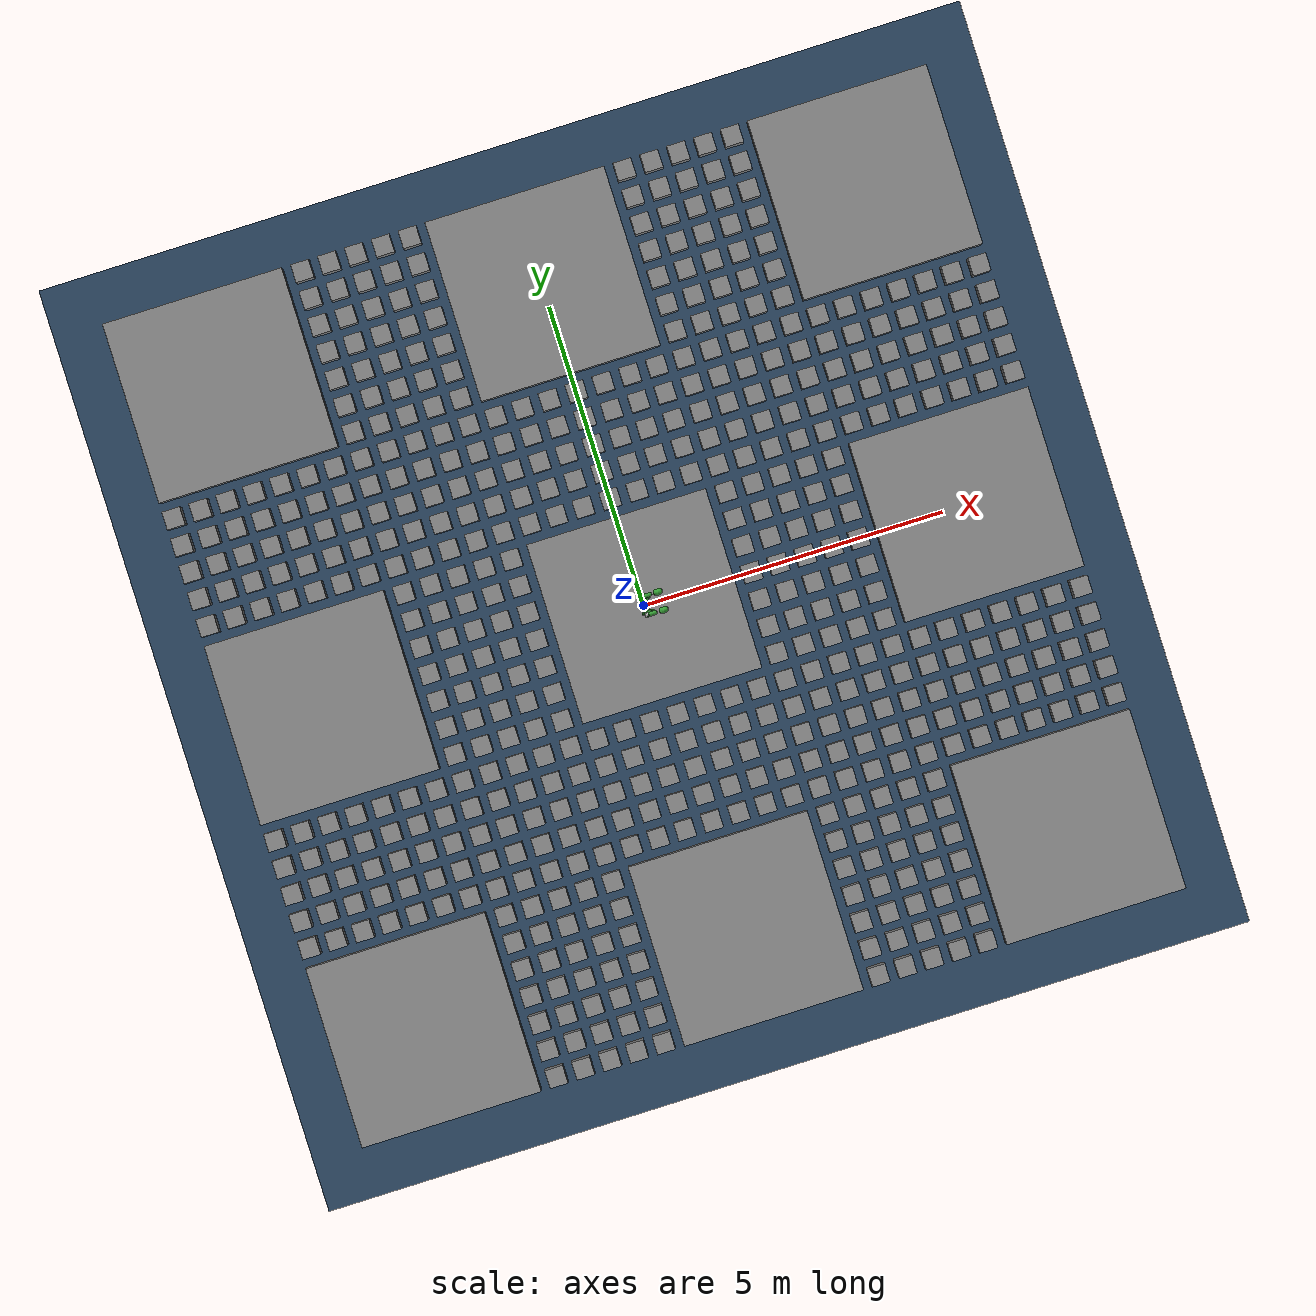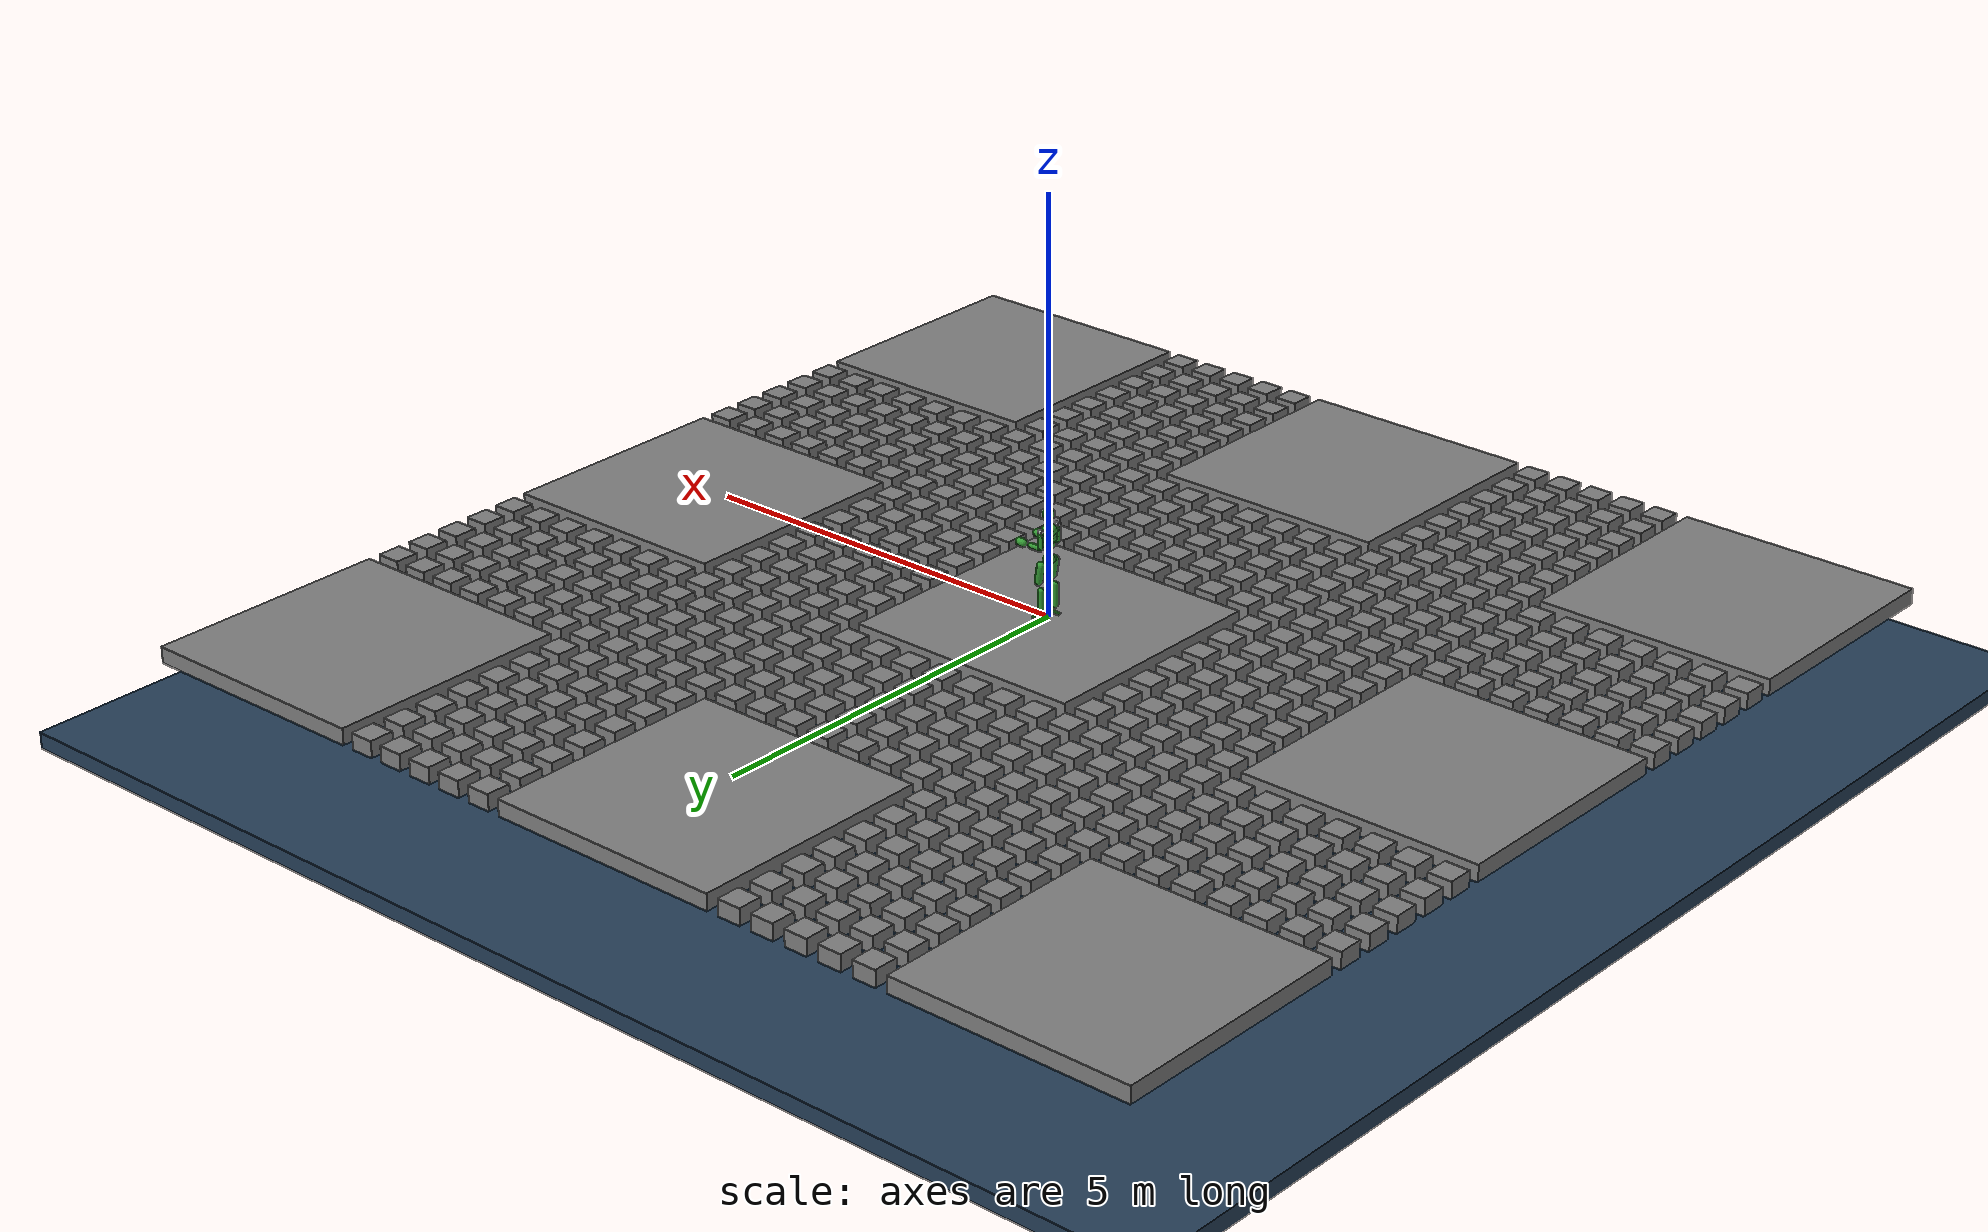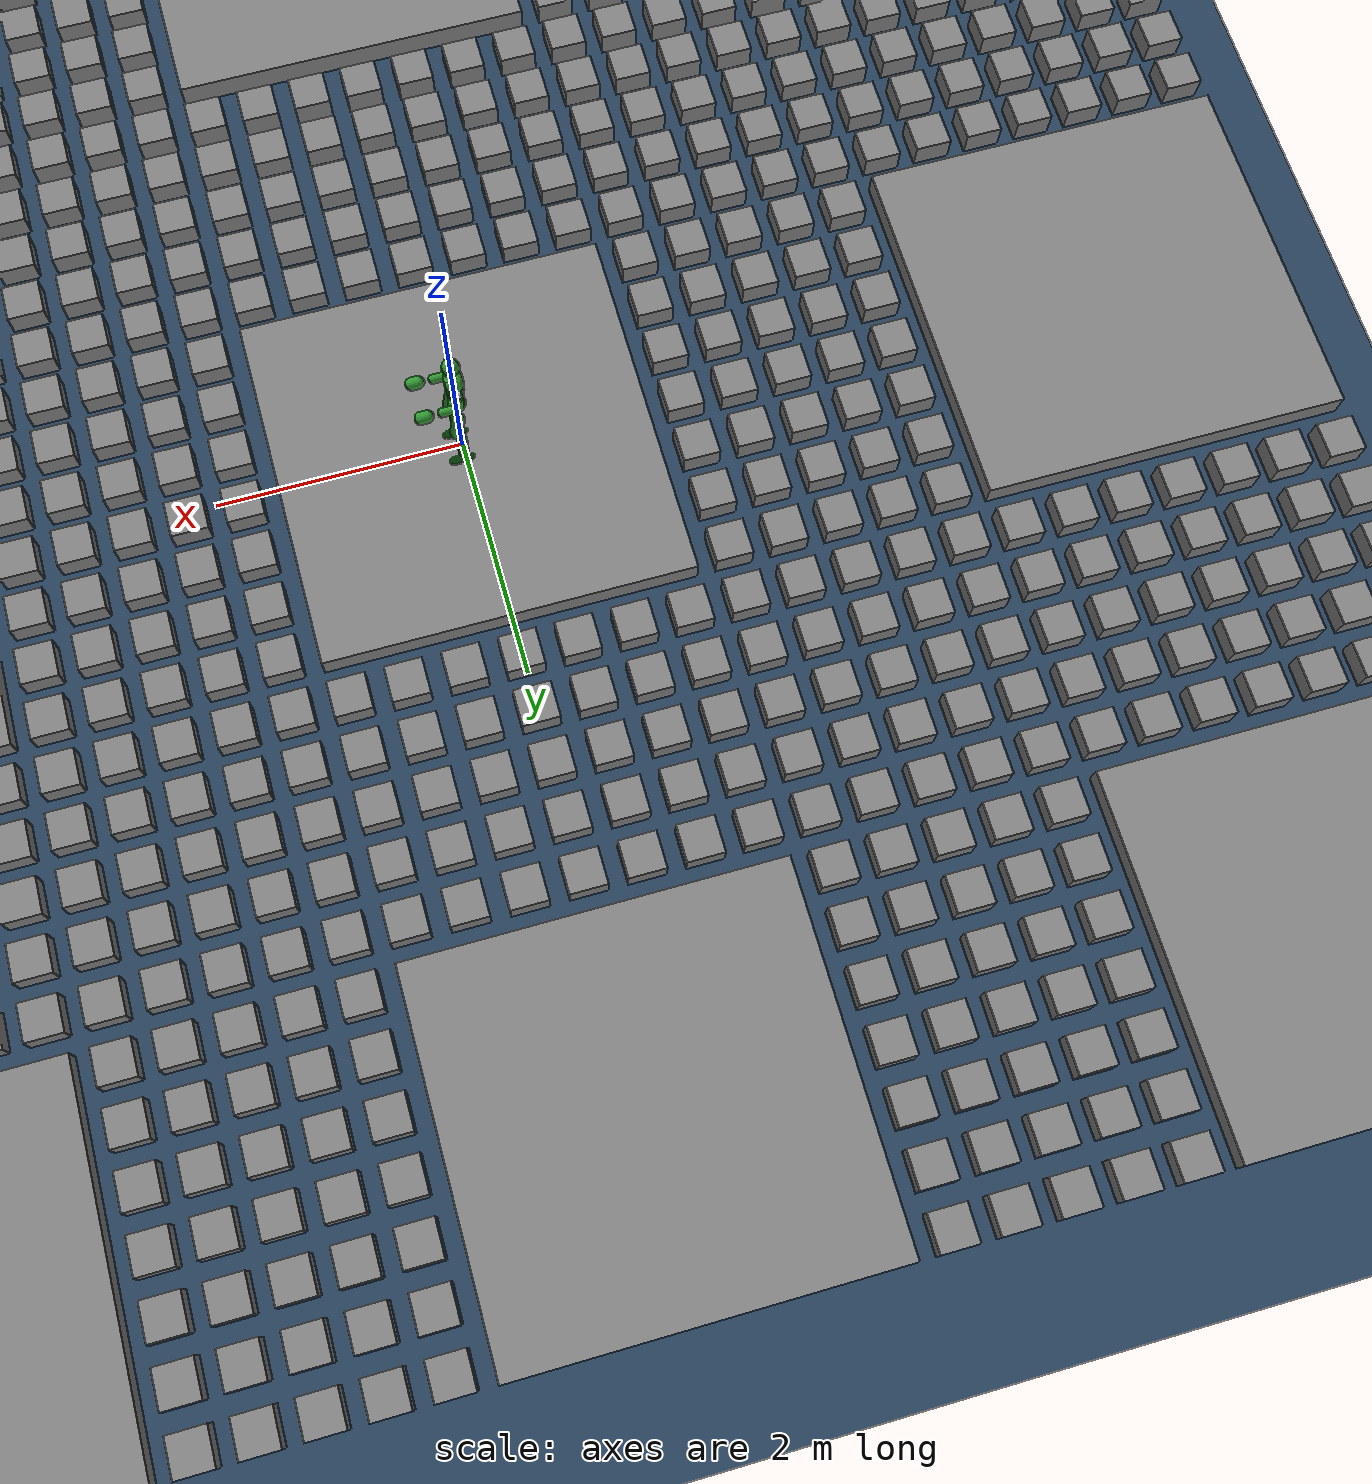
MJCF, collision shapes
<mujoco model="g1_29dof scene">
    <include file="../g1_29dof.xml"/>
    <option timestep="0.002" iterations="50" solver="Newton"/>
    <compiler angle="radian" meshdir="../meshes/"/>

    <visual>
        <headlight diffuse="0.6 0.6 0.6" ambient="0.3 0.3 0.3" specular="0 0 0"/>
        <rgba haze="0.15 0.25 0.35 1"/>
        <global azimuth="120" elevation="-20"/>
    </visual>

    <statistic center="0 0 0.5" extent="2.0"/>

    <asset>
        <texture type="skybox" builtin="gradient" rgb1="0.3 0.5 0.7" rgb2="0 0 0" width="512" height="3072"/>
        <texture type="2d" name="groundplane" builtin="checker" mark="edge" rgb1="0.2 0.3 0.4" rgb2="0.1 0.2 0.3"
                markrgb="0.8 0.8 0.8" width="300" height="300"/>
        <material name="groundplane" texture="groundplane" texuniform="true" texrepeat="5 5" reflectance="0.2"/>
    </asset>

    <worldbody>
        <light pos="0 0 1.5" dir="0 0 -1" directional="true"/>

        <!-- Center Lower Platform -->
        <geom name="floor" pos="0.0 0.0 -1.1" type="box" size="100.0 100.0 0.1" quat="1 0 0 0" group="2" margin="0.01" solimp="0.99 0.99 0.01" solref="0.005 1" material="groundplane"/>

        <!-- Center Upper Platform -->
        <geom pos="0.0 0.0 -0.1" type="box" size="1.5 1.5 0.1" quat="1 0 0 0" group="2" margin="0.01" solimp="0.99 0.99 0.01" solref="0.005 1"/>

        <!-- Rightward stepping stone-->
        <geom pos="1.8 6.75 -0.1" type="box" size="0.15 0.15 0.1" quat="1 0 0 0" group="2" margin="0.01" solimp="0.99 0.99 0.01" solref="0.005 1"/>
        <geom pos="1.8 6.3 -0.1" type="box" size="0.15 0.15 0.1" quat="1 0 0 0" group="2" margin="0.01" solimp="0.99 0.99 0.01" solref="0.005 1"/>
        <geom pos="1.8 5.85 -0.1" type="box" size="0.15 0.15 0.1" quat="1 0 0 0" group="2" margin="0.01" solimp="0.99 0.99 0.01" solref="0.005 1"/>
        <geom pos="1.8 5.4 -0.1" type="box" size="0.15 0.15 0.1" quat="1 0 0 0" group="2" margin="0.01" solimp="0.99 0.99 0.01" solref="0.005 1"/>
        <geom pos="1.8 4.95 -0.1" type="box" size="0.15 0.15 0.1" quat="1 0 0 0" group="2" margin="0.01" solimp="0.99 0.99 0.01" solref="0.005 1"/>
        <geom pos="1.8 4.5 -0.1" type="box" size="0.15 0.15 0.1" quat="1 0 0 0" group="2" margin="0.01" solimp="0.99 0.99 0.01" solref="0.005 1"/>
        <geom pos="1.8 4.05 -0.1" type="box" size="0.15 0.15 0.1" quat="1 0 0 0" group="2" margin="0.01" solimp="0.99 0.99 0.01" solref="0.005 1"/>
        <geom pos="1.8 3.6 -0.1" type="box" size="0.15 0.15 0.1" quat="1 0 0 0" group="2" margin="0.01" solimp="0.99 0.99 0.01" solref="0.005 1"/>
        <geom pos="1.8 3.15 -0.1" type="box" size="0.15 0.15 0.1" quat="1 0 0 0" group="2" margin="0.01" solimp="0.99 0.99 0.01" solref="0.005 1"/>
        <geom pos="1.8 2.7 -0.1" type="box" size="0.15 0.15 0.1" quat="1 0 0 0" group="2" margin="0.01" solimp="0.99 0.99 0.01" solref="0.005 1"/>
        <geom pos="1.8 2.25 -0.1" type="box" size="0.15 0.15 0.1" quat="1 0 0 0" group="2" margin="0.01" solimp="0.99 0.99 0.01" solref="0.005 1"/>
        <geom pos="1.8 1.8 -0.1" type="box" size="0.15 0.15 0.1" quat="1 0 0 0" group="2" margin="0.01" solimp="0.99 0.99 0.01" solref="0.005 1"/>
        <geom pos="1.8 1.35 -0.1" type="box" size="0.15 0.15 0.1" quat="1 0 0 0" group="2" margin="0.01" solimp="0.99 0.99 0.01" solref="0.005 1"/>
        <geom pos="1.8 0.9 -0.1" type="box" size="0.15 0.15 0.1" quat="1 0 0 0" group="2" margin="0.01" solimp="0.99 0.99 0.01" solref="0.005 1"/>
        <geom pos="1.8 0.45 -0.1" type="box" size="0.15 0.15 0.1" quat="1 0 0 0" group="2" margin="0.01" solimp="0.99 0.99 0.01" solref="0.005 1"/>
        <geom pos="1.8 0.0 -0.1" type="box" size="0.15 0.15 0.1" quat="1 0 0 0" group="2" margin="0.01" solimp="0.99 0.99 0.01" solref="0.005 1"/>
        <geom pos="1.8 -0.45 -0.1" type="box" size="0.15 0.15 0.1" quat="1 0 0 0" group="2" margin="0.01" solimp="0.99 0.99 0.01" solref="0.005 1"/>
        <geom pos="1.8 -0.9 -0.1" type="box" size="0.15 0.15 0.1" quat="1 0 0 0" group="2" margin="0.01" solimp="0.99 0.99 0.01" solref="0.005 1"/>
        <geom pos="1.8 -1.35 -0.1" type="box" size="0.15 0.15 0.1" quat="1 0 0 0" group="2" margin="0.01" solimp="0.99 0.99 0.01" solref="0.005 1"/>
        <geom pos="1.8 -1.8 -0.1" type="box" size="0.15 0.15 0.1" quat="1 0 0 0" group="2" margin="0.01" solimp="0.99 0.99 0.01" solref="0.005 1"/>
        <geom pos="1.8 -2.25 -0.1" type="box" size="0.15 0.15 0.1" quat="1 0 0 0" group="2" margin="0.01" solimp="0.99 0.99 0.01" solref="0.005 1"/>
        <geom pos="1.8 -2.7 -0.1" type="box" size="0.15 0.15 0.1" quat="1 0 0 0" group="2" margin="0.01" solimp="0.99 0.99 0.01" solref="0.005 1"/>
        <geom pos="1.8 -3.15 -0.1" type="box" size="0.15 0.15 0.1" quat="1 0 0 0" group="2" margin="0.01" solimp="0.99 0.99 0.01" solref="0.005 1"/>
        <geom pos="1.8 -3.6 -0.1" type="box" size="0.15 0.15 0.1" quat="1 0 0 0" group="2" margin="0.01" solimp="0.99 0.99 0.01" solref="0.005 1"/>
        <geom pos="1.8 -4.05 -0.1" type="box" size="0.15 0.15 0.1" quat="1 0 0 0" group="2" margin="0.01" solimp="0.99 0.99 0.01" solref="0.005 1"/>
        <geom pos="1.8 -4.5 -0.1" type="box" size="0.15 0.15 0.1" quat="1 0 0 0" group="2" margin="0.01" solimp="0.99 0.99 0.01" solref="0.005 1"/>
        <geom pos="1.8 -4.95 -0.1" type="box" size="0.15 0.15 0.1" quat="1 0 0 0" group="2" margin="0.01" solimp="0.99 0.99 0.01" solref="0.005 1"/>
        <geom pos="1.8 -5.4 -0.1" type="box" size="0.15 0.15 0.1" quat="1 0 0 0" group="2" margin="0.01" solimp="0.99 0.99 0.01" solref="0.005 1"/>
        <geom pos="1.8 -5.85 -0.1" type="box" size="0.15 0.15 0.1" quat="1 0 0 0" group="2" margin="0.01" solimp="0.99 0.99 0.01" solref="0.005 1"/>
        <geom pos="1.8 -6.3 -0.1" type="box" size="0.15 0.15 0.1" quat="1 0 0 0" group="2" margin="0.01" solimp="0.99 0.99 0.01" solref="0.005 1"/>
        <geom pos="1.8 -6.75 -0.1" type="box" size="0.15 0.15 0.1" quat="1 0 0 0" group="2" margin="0.01" solimp="0.99 0.99 0.01" solref="0.005 1"/>

        <geom pos="2.25 6.75 -0.1" type="box" size="0.15 0.15 0.1" quat="1 0 0 0" group="2" margin="0.01" solimp="0.99 0.99 0.01" solref="0.005 1"/>
        <geom pos="2.25 6.3 -0.1" type="box" size="0.15 0.15 0.1" quat="1 0 0 0" group="2" margin="0.01" solimp="0.99 0.99 0.01" solref="0.005 1"/>
        <geom pos="2.25 5.85 -0.1" type="box" size="0.15 0.15 0.1" quat="1 0 0 0" group="2" margin="0.01" solimp="0.99 0.99 0.01" solref="0.005 1"/>
        <geom pos="2.25 5.4 -0.1" type="box" size="0.15 0.15 0.1" quat="1 0 0 0" group="2" margin="0.01" solimp="0.99 0.99 0.01" solref="0.005 1"/>
        <geom pos="2.25 4.95 -0.1" type="box" size="0.15 0.15 0.1" quat="1 0 0 0" group="2" margin="0.01" solimp="0.99 0.99 0.01" solref="0.005 1"/>
        <geom pos="2.25 4.5 -0.1" type="box" size="0.15 0.15 0.1" quat="1 0 0 0" group="2" margin="0.01" solimp="0.99 0.99 0.01" solref="0.005 1"/>
        <geom pos="2.25 4.05 -0.1" type="box" size="0.15 0.15 0.1" quat="1 0 0 0" group="2" margin="0.01" solimp="0.99 0.99 0.01" solref="0.005 1"/>
        <geom pos="2.25 3.6 -0.1" type="box" size="0.15 0.15 0.1" quat="1 0 0 0" group="2" margin="0.01" solimp="0.99 0.99 0.01" solref="0.005 1"/>
        <geom pos="2.25 3.15 -0.1" type="box" size="0.15 0.15 0.1" quat="1 0 0 0" group="2" margin="0.01" solimp="0.99 0.99 0.01" solref="0.005 1"/>
        <geom pos="2.25 2.7 -0.1" type="box" size="0.15 0.15 0.1" quat="1 0 0 0" group="2" margin="0.01" solimp="0.99 0.99 0.01" solref="0.005 1"/>
        <geom pos="2.25 2.25 -0.1" type="box" size="0.15 0.15 0.1" quat="1 0 0 0" group="2" margin="0.01" solimp="0.99 0.99 0.01" solref="0.005 1"/>
        <geom pos="2.25 1.8 -0.1" type="box" size="0.15 0.15 0.1" quat="1 0 0 0" group="2" margin="0.01" solimp="0.99 0.99 0.01" solref="0.005 1"/>
        <geom pos="2.25 1.35 -0.1" type="box" size="0.15 0.15 0.1" quat="1 0 0 0" group="2" margin="0.01" solimp="0.99 0.99 0.01" solref="0.005 1"/>
        <geom pos="2.25 0.9 -0.1" type="box" size="0.15 0.15 0.1" quat="1 0 0 0" group="2" margin="0.01" solimp="0.99 0.99 0.01" solref="0.005 1"/>
        <geom pos="2.25 0.45 -0.1" type="box" size="0.15 0.15 0.1" quat="1 0 0 0" group="2" margin="0.01" solimp="0.99 0.99 0.01" solref="0.005 1"/>
        <geom pos="2.25 0.0 -0.1" type="box" size="0.15 0.15 0.1" quat="1 0 0 0" group="2" margin="0.01" solimp="0.99 0.99 0.01" solref="0.005 1"/>
        <geom pos="2.25 -0.45 -0.1" type="box" size="0.15 0.15 0.1" quat="1 0 0 0" group="2" margin="0.01" solimp="0.99 0.99 0.01" solref="0.005 1"/>
        <geom pos="2.25 -0.9 -0.1" type="box" size="0.15 0.15 0.1" quat="1 0 0 0" group="2" margin="0.01" solimp="0.99 0.99 0.01" solref="0.005 1"/>
        <geom pos="2.25 -1.35 -0.1" type="box" size="0.15 0.15 0.1" quat="1 0 0 0" group="2" margin="0.01" solimp="0.99 0.99 0.01" solref="0.005 1"/>
        <geom pos="2.25 -1.8 -0.1" type="box" size="0.15 0.15 0.1" quat="1 0 0 0" group="2" margin="0.01" solimp="0.99 0.99 0.01" solref="0.005 1"/>
        <geom pos="2.25 -2.25 -0.1" type="box" size="0.15 0.15 0.1" quat="1 0 0 0" group="2" margin="0.01" solimp="0.99 0.99 0.01" solref="0.005 1"/>
        <geom pos="2.25 -2.7 -0.1" type="box" size="0.15 0.15 0.1" quat="1 0 0 0" group="2" margin="0.01" solimp="0.99 0.99 0.01" solref="0.005 1"/>
        <geom pos="2.25 -3.15 -0.1" type="box" size="0.15 0.15 0.1" quat="1 0 0 0" group="2" margin="0.01" solimp="0.99 0.99 0.01" solref="0.005 1"/>
        <geom pos="2.25 -3.6 -0.1" type="box" size="0.15 0.15 0.1" quat="1 0 0 0" group="2" margin="0.01" solimp="0.99 0.99 0.01" solref="0.005 1"/>
        <geom pos="2.25 -4.05 -0.1" type="box" size="0.15 0.15 0.1" quat="1 0 0 0" group="2" margin="0.01" solimp="0.99 0.99 0.01" solref="0.005 1"/>
        <geom pos="2.25 -4.5 -0.1" type="box" size="0.15 0.15 0.1" quat="1 0 0 0" group="2" margin="0.01" solimp="0.99 0.99 0.01" solref="0.005 1"/>
        <geom pos="2.25 -4.95 -0.1" type="box" size="0.15 0.15 0.1" quat="1 0 0 0" group="2" margin="0.01" solimp="0.99 0.99 0.01" solref="0.005 1"/>
        <geom pos="2.25 -5.4 -0.1" type="box" size="0.15 0.15 0.1" quat="1 0 0 0" group="2" margin="0.01" solimp="0.99 0.99 0.01" solref="0.005 1"/>
        <geom pos="2.25 -5.85 -0.1" type="box" size="0.15 0.15 0.1" quat="1 0 0 0" group="2" margin="0.01" solimp="0.99 0.99 0.01" solref="0.005 1"/>
        <geom pos="2.25 -6.3 -0.1" type="box" size="0.15 0.15 0.1" quat="1 0 0 0" group="2" margin="0.01" solimp="0.99 0.99 0.01" solref="0.005 1"/>
        <geom pos="2.25 -6.75 -0.1" type="box" size="0.15 0.15 0.1" quat="1 0 0 0" group="2" margin="0.01" solimp="0.99 0.99 0.01" solref="0.005 1"/>

        <geom pos="2.7 6.75 -0.1" type="box" size="0.15 0.15 0.1" quat="1 0 0 0" group="2" margin="0.01" solimp="0.99 0.99 0.01" solref="0.005 1"/>
        <geom pos="2.7 6.3 -0.1" type="box" size="0.15 0.15 0.1" quat="1 0 0 0" group="2" margin="0.01" solimp="0.99 0.99 0.01" solref="0.005 1"/>
        <geom pos="2.7 5.85 -0.1" type="box" size="0.15 0.15 0.1" quat="1 0 0 0" group="2" margin="0.01" solimp="0.99 0.99 0.01" solref="0.005 1"/>
        <geom pos="2.7 5.4 -0.1" type="box" size="0.15 0.15 0.1" quat="1 0 0 0" group="2" margin="0.01" solimp="0.99 0.99 0.01" solref="0.005 1"/>
        <geom pos="2.7 4.95 -0.1" type="box" size="0.15 0.15 0.1" quat="1 0 0 0" group="2" margin="0.01" solimp="0.99 0.99 0.01" solref="0.005 1"/>
        <geom pos="2.7 4.5 -0.1" type="box" size="0.15 0.15 0.1" quat="1 0 0 0" group="2" margin="0.01" solimp="0.99 0.99 0.01" solref="0.005 1"/>
        <geom pos="2.7 4.05 -0.1" type="box" size="0.15 0.15 0.1" quat="1 0 0 0" group="2" margin="0.01" solimp="0.99 0.99 0.01" solref="0.005 1"/>
        <geom pos="2.7 3.6 -0.1" type="box" size="0.15 0.15 0.1" quat="1 0 0 0" group="2" margin="0.01" solimp="0.99 0.99 0.01" solref="0.005 1"/>
        <geom pos="2.7 3.15 -0.1" type="box" size="0.15 0.15 0.1" quat="1 0 0 0" group="2" margin="0.01" solimp="0.99 0.99 0.01" solref="0.005 1"/>
        <geom pos="2.7 2.7 -0.1" type="box" size="0.15 0.15 0.1" quat="1 0 0 0" group="2" margin="0.01" solimp="0.99 0.99 0.01" solref="0.005 1"/>
        <geom pos="2.7 2.25 -0.1" type="box" size="0.15 0.15 0.1" quat="1 0 0 0" group="2" margin="0.01" solimp="0.99 0.99 0.01" solref="0.005 1"/>
        <geom pos="2.7 1.8 -0.1" type="box" size="0.15 0.15 0.1" quat="1 0 0 0" group="2" margin="0.01" solimp="0.99 0.99 0.01" solref="0.005 1"/>
        <geom pos="2.7 1.35 -0.1" type="box" size="0.15 0.15 0.1" quat="1 0 0 0" group="2" margin="0.01" solimp="0.99 0.99 0.01" solref="0.005 1"/>
        <geom pos="2.7 0.9 -0.1" type="box" size="0.15 0.15 0.1" quat="1 0 0 0" group="2" margin="0.01" solimp="0.99 0.99 0.01" solref="0.005 1"/>
        <geom pos="2.7 0.45 -0.1" type="box" size="0.15 0.15 0.1" quat="1 0 0 0" group="2" margin="0.01" solimp="0.99 0.99 0.01" solref="0.005 1"/>
        <geom pos="2.7 0.0 -0.1" type="box" size="0.15 0.15 0.1" quat="1 0 0 0" group="2" margin="0.01" solimp="0.99 0.99 0.01" solref="0.005 1"/>
        <geom pos="2.7 -0.45 -0.1" type="box" size="0.15 0.15 0.1" quat="1 0 0 0" group="2" margin="0.01" solimp="0.99 0.99 0.01" solref="0.005 1"/>
        <geom pos="2.7 -0.9 -0.1" type="box" size="0.15 0.15 0.1" quat="1 0 0 0" group="2" margin="0.01" solimp="0.99 0.99 0.01" solref="0.005 1"/>
        <geom pos="2.7 -1.35 -0.1" type="box" size="0.15 0.15 0.1" quat="1 0 0 0" group="2" margin="0.01" solimp="0.99 0.99 0.01" solref="0.005 1"/>
        <geom pos="2.7 -1.8 -0.1" type="box" size="0.15 0.15 0.1" quat="1 0 0 0" group="2" margin="0.01" solimp="0.99 0.99 0.01" solref="0.005 1"/>
        <geom pos="2.7 -2.25 -0.1" type="box" size="0.15 0.15 0.1" quat="1 0 0 0" group="2" margin="0.01" solimp="0.99 0.99 0.01" solref="0.005 1"/>
        <geom pos="2.7 -2.7 -0.1" type="box" size="0.15 0.15 0.1" quat="1 0 0 0" group="2" margin="0.01" solimp="0.99 0.99 0.01" solref="0.005 1"/>
        <geom pos="2.7 -3.15 -0.1" type="box" size="0.15 0.15 0.1" quat="1 0 0 0" group="2" margin="0.01" solimp="0.99 0.99 0.01" solref="0.005 1"/>
        <geom pos="2.7 -3.6 -0.1" type="box" size="0.15 0.15 0.1" quat="1 0 0 0" group="2" margin="0.01" solimp="0.99 0.99 0.01" solref="0.005 1"/>
        <geom pos="2.7 -4.05 -0.1" type="box" size="0.15 0.15 0.1" quat="1 0 0 0" group="2" margin="0.01" solimp="0.99 0.99 0.01" solref="0.005 1"/>
        <geom pos="2.7 -4.5 -0.1" type="box" size="0.15 0.15 0.1" quat="1 0 0 0" group="2" margin="0.01" solimp="0.99 0.99 0.01" solref="0.005 1"/>
        <geom pos="2.7 -4.95 -0.1" type="box" size="0.15 0.15 0.1" quat="1 0 0 0" group="2" margin="0.01" solimp="0.99 0.99 0.01" solref="0.005 1"/>
        <geom pos="2.7 -5.4 -0.1" type="box" size="0.15 0.15 0.1" quat="1 0 0 0" group="2" margin="0.01" solimp="0.99 0.99 0.01" solref="0.005 1"/>
        <geom pos="2.7 -5.85 -0.1" type="box" size="0.15 0.15 0.1" quat="1 0 0 0" group="2" margin="0.01" solimp="0.99 0.99 0.01" solref="0.005 1"/>
        <geom pos="2.7 -6.3 -0.1" type="box" size="0.15 0.15 0.1" quat="1 0 0 0" group="2" margin="0.01" solimp="0.99 0.99 0.01" solref="0.005 1"/>
        <geom pos="2.7 -6.75 -0.1" type="box" size="0.15 0.15 0.1" quat="1 0 0 0" group="2" margin="0.01" solimp="0.99 0.99 0.01" solref="0.005 1"/>

        <geom pos="3.15 6.75 -0.1" type="box" size="0.15 0.15 0.1" quat="1 0 0 0" group="2" margin="0.01" solimp="0.99 0.99 0.01" solref="0.005 1"/>
        <geom pos="3.15 6.3 -0.1" type="box" size="0.15 0.15 0.1" quat="1 0 0 0" group="2" margin="0.01" solimp="0.99 0.99 0.01" solref="0.005 1"/>
        <geom pos="3.15 5.85 -0.1" type="box" size="0.15 0.15 0.1" quat="1 0 0 0" group="2" margin="0.01" solimp="0.99 0.99 0.01" solref="0.005 1"/>
        <geom pos="3.15 5.4 -0.1" type="box" size="0.15 0.15 0.1" quat="1 0 0 0" group="2" margin="0.01" solimp="0.99 0.99 0.01" solref="0.005 1"/>
        <geom pos="3.15 4.95 -0.1" type="box" size="0.15 0.15 0.1" quat="1 0 0 0" group="2" margin="0.01" solimp="0.99 0.99 0.01" solref="0.005 1"/>
        <geom pos="3.15 4.5 -0.1" type="box" size="0.15 0.15 0.1" quat="1 0 0 0" group="2" margin="0.01" solimp="0.99 0.99 0.01" solref="0.005 1"/>
        <geom pos="3.15 4.05 -0.1" type="box" size="0.15 0.15 0.1" quat="1 0 0 0" group="2" margin="0.01" solimp="0.99 0.99 0.01" solref="0.005 1"/>
        <geom pos="3.15 3.6 -0.1" type="box" size="0.15 0.15 0.1" quat="1 0 0 0" group="2" margin="0.01" solimp="0.99 0.99 0.01" solref="0.005 1"/>
        <geom pos="3.15 3.15 -0.1" type="box" size="0.15 0.15 0.1" quat="1 0 0 0" group="2" margin="0.01" solimp="0.99 0.99 0.01" solref="0.005 1"/>
        <geom pos="3.15 2.7 -0.1" type="box" size="0.15 0.15 0.1" quat="1 0 0 0" group="2" margin="0.01" solimp="0.99 0.99 0.01" solref="0.005 1"/>
        <geom pos="3.15 2.25 -0.1" type="box" size="0.15 0.15 0.1" quat="1 0 0 0" group="2" margin="0.01" solimp="0.99 0.99 0.01" solref="0.005 1"/>
        <geom pos="3.15 1.8 -0.1" type="box" size="0.15 0.15 0.1" quat="1 0 0 0" group="2" margin="0.01" solimp="0.99 0.99 0.01" solref="0.005 1"/>
        <geom pos="3.15 1.35 -0.1" type="box" size="0.15 0.15 0.1" quat="1 0 0 0" group="2" margin="0.01" solimp="0.99 0.99 0.01" solref="0.005 1"/>
        <geom pos="3.15 0.9 -0.1" type="box" size="0.15 0.15 0.1" quat="1 0 0 0" group="2" margin="0.01" solimp="0.99 0.99 0.01" solref="0.005 1"/>
        <geom pos="3.15 0.45 -0.1" type="box" size="0.15 0.15 0.1" quat="1 0 0 0" group="2" margin="0.01" solimp="0.99 0.99 0.01" solref="0.005 1"/>
        <geom pos="3.15 0.0 -0.1" type="box" size="0.15 0.15 0.1" quat="1 0 0 0" group="2" margin="0.01" solimp="0.99 0.99 0.01" solref="0.005 1"/>
        <geom pos="3.15 -0.45 -0.1" type="box" size="0.15 0.15 0.1" quat="1 0 0 0" group="2" margin="0.01" solimp="0.99 0.99 0.01" solref="0.005 1"/>
        <geom pos="3.15 -0.9 -0.1" type="box" size="0.15 0.15 0.1" quat="1 0 0 0" group="2" margin="0.01" solimp="0.99 0.99 0.01" solref="0.005 1"/>
        <geom pos="3.15 -1.35 -0.1" type="box" size="0.15 0.15 0.1" quat="1 0 0 0" group="2" margin="0.01" solimp="0.99 0.99 0.01" solref="0.005 1"/>
        <geom pos="3.15 -1.8 -0.1" type="box" size="0.15 0.15 0.1" quat="1 0 0 0" group="2" margin="0.01" solimp="0.99 0.99 0.01" solref="0.005 1"/>
        <geom pos="3.15 -2.25 -0.1" type="box" size="0.15 0.15 0.1" quat="1 0 0 0" group="2" margin="0.01" solimp="0.99 0.99 0.01" solref="0.005 1"/>
        <geom pos="3.15 -2.7 -0.1" type="box" size="0.15 0.15 0.1" quat="1 0 0 0" group="2" margin="0.01" solimp="0.99 0.99 0.01" solref="0.005 1"/>
        <geom pos="3.15 -3.15 -0.1" type="box" size="0.15 0.15 0.1" quat="1 0 0 0" group="2" margin="0.01" solimp="0.99 0.99 0.01" solref="0.005 1"/>
        <geom pos="3.15 -3.6 -0.1" type="box" size="0.15 0.15 0.1" quat="1 0 0 0" group="2" margin="0.01" solimp="0.99 0.99 0.01" solref="0.005 1"/>
        <geom pos="3.15 -4.05 -0.1" type="box" size="0.15 0.15 0.1" quat="1 0 0 0" group="2" margin="0.01" solimp="0.99 0.99 0.01" solref="0.005 1"/>
        <geom pos="3.15 -4.5 -0.1" type="box" size="0.15 0.15 0.1" quat="1 0 0 0" group="2" margin="0.01" solimp="0.99 0.99 0.01" solref="0.005 1"/>
        <geom pos="3.15 -4.95 -0.1" type="box" size="0.15 0.15 0.1" quat="1 0 0 0" group="2" margin="0.01" solimp="0.99 0.99 0.01" solref="0.005 1"/>
        <geom pos="3.15 -5.4 -0.1" type="box" size="0.15 0.15 0.1" quat="1 0 0 0" group="2" margin="0.01" solimp="0.99 0.99 0.01" solref="0.005 1"/>
        <geom pos="3.15 -5.85 -0.1" type="box" size="0.15 0.15 0.1" quat="1 0 0 0" group="2" margin="0.01" solimp="0.99 0.99 0.01" solref="0.005 1"/>
        <geom pos="3.15 -6.3 -0.1" type="box" size="0.15 0.15 0.1" quat="1 0 0 0" group="2" margin="0.01" solimp="0.99 0.99 0.01" solref="0.005 1"/>
        <geom pos="3.15 -6.75 -0.1" type="box" size="0.15 0.15 0.1" quat="1 0 0 0" group="2" margin="0.01" solimp="0.99 0.99 0.01" solref="0.005 1"/>

        <geom pos="3.6 6.75 -0.1" type="box" size="0.15 0.15 0.1" quat="1 0 0 0" group="2" margin="0.01" solimp="0.99 0.99 0.01" solref="0.005 1"/>
        <geom pos="3.6 6.3 -0.1" type="box" size="0.15 0.15 0.1" quat="1 0 0 0" group="2" margin="0.01" solimp="0.99 0.99 0.01" solref="0.005 1"/>
        <geom pos="3.6 5.85 -0.1" type="box" size="0.15 0.15 0.1" quat="1 0 0 0" group="2" margin="0.01" solimp="0.99 0.99 0.01" solref="0.005 1"/>
        <geom pos="3.6 5.4 -0.1" type="box" size="0.15 0.15 0.1" quat="1 0 0 0" group="2" margin="0.01" solimp="0.99 0.99 0.01" solref="0.005 1"/>
        <geom pos="3.6 4.95 -0.1" type="box" size="0.15 0.15 0.1" quat="1 0 0 0" group="2" margin="0.01" solimp="0.99 0.99 0.01" solref="0.005 1"/>
        <geom pos="3.6 4.5 -0.1" type="box" size="0.15 0.15 0.1" quat="1 0 0 0" group="2" margin="0.01" solimp="0.99 0.99 0.01" solref="0.005 1"/>
        <geom pos="3.6 4.05 -0.1" type="box" size="0.15 0.15 0.1" quat="1 0 0 0" group="2" margin="0.01" solimp="0.99 0.99 0.01" solref="0.005 1"/>
        <geom pos="3.6 3.6 -0.1" type="box" size="0.15 0.15 0.1" quat="1 0 0 0" group="2" margin="0.01" solimp="0.99 0.99 0.01" solref="0.005 1"/>
        <geom pos="3.6 3.15 -0.1" type="box" size="0.15 0.15 0.1" quat="1 0 0 0" group="2" margin="0.01" solimp="0.99 0.99 0.01" solref="0.005 1"/>
        <geom pos="3.6 2.7 -0.1" type="box" size="0.15 0.15 0.1" quat="1 0 0 0" group="2" margin="0.01" solimp="0.99 0.99 0.01" solref="0.005 1"/>
        <geom pos="3.6 2.25 -0.1" type="box" size="0.15 0.15 0.1" quat="1 0 0 0" group="2" margin="0.01" solimp="0.99 0.99 0.01" solref="0.005 1"/>
        <geom pos="3.6 1.8 -0.1" type="box" size="0.15 0.15 0.1" quat="1 0 0 0" group="2" margin="0.01" solimp="0.99 0.99 0.01" solref="0.005 1"/>
        <geom pos="3.6 1.35 -0.1" type="box" size="0.15 0.15 0.1" quat="1 0 0 0" group="2" margin="0.01" solimp="0.99 0.99 0.01" solref="0.005 1"/>
        <geom pos="3.6 0.9 -0.1" type="box" size="0.15 0.15 0.1" quat="1 0 0 0" group="2" margin="0.01" solimp="0.99 0.99 0.01" solref="0.005 1"/>
        <geom pos="3.6 0.45 -0.1" type="box" size="0.15 0.15 0.1" quat="1 0 0 0" group="2" margin="0.01" solimp="0.99 0.99 0.01" solref="0.005 1"/>
        <geom pos="3.6 0.0 -0.1" type="box" size="0.15 0.15 0.1" quat="1 0 0 0" group="2" margin="0.01" solimp="0.99 0.99 0.01" solref="0.005 1"/>
        <geom pos="3.6 -0.45 -0.1" type="box" size="0.15 0.15 0.1" quat="1 0 0 0" group="2" margin="0.01" solimp="0.99 0.99 0.01" solref="0.005 1"/>
        <geom pos="3.6 -0.9 -0.1" type="box" size="0.15 0.15 0.1" quat="1 0 0 0" group="2" margin="0.01" solimp="0.99 0.99 0.01" solref="0.005 1"/>
        <geom pos="3.6 -1.35 -0.1" type="box" size="0.15 0.15 0.1" quat="1 0 0 0" group="2" margin="0.01" solimp="0.99 0.99 0.01" solref="0.005 1"/>
        <geom pos="3.6 -1.8 -0.1" type="box" size="0.15 0.15 0.1" quat="1 0 0 0" group="2" margin="0.01" solimp="0.99 0.99 0.01" solref="0.005 1"/>
        <geom pos="3.6 -2.25 -0.1" type="box" size="0.15 0.15 0.1" quat="1 0 0 0" group="2" margin="0.01" solimp="0.99 0.99 0.01" solref="0.005 1"/>
        <geom pos="3.6 -2.7 -0.1" type="box" size="0.15 0.15 0.1" quat="1 0 0 0" group="2" margin="0.01" solimp="0.99 0.99 0.01" solref="0.005 1"/>
        <geom pos="3.6 -3.15 -0.1" type="box" size="0.15 0.15 0.1" quat="1 0 0 0" group="2" margin="0.01" solimp="0.99 0.99 0.01" solref="0.005 1"/>
        <geom pos="3.6 -3.6 -0.1" type="box" size="0.15 0.15 0.1" quat="1 0 0 0" group="2" margin="0.01" solimp="0.99 0.99 0.01" solref="0.005 1"/>
        <geom pos="3.6 -4.05 -0.1" type="box" size="0.15 0.15 0.1" quat="1 0 0 0" group="2" margin="0.01" solimp="0.99 0.99 0.01" solref="0.005 1"/>
        <geom pos="3.6 -4.5 -0.1" type="box" size="0.15 0.15 0.1" quat="1 0 0 0" group="2" margin="0.01" solimp="0.99 0.99 0.01" solref="0.005 1"/>
        <geom pos="3.6 -4.95 -0.1" type="box" size="0.15 0.15 0.1" quat="1 0 0 0" group="2" margin="0.01" solimp="0.99 0.99 0.01" solref="0.005 1"/>
        <geom pos="3.6 -5.4 -0.1" type="box" size="0.15 0.15 0.1" quat="1 0 0 0" group="2" margin="0.01" solimp="0.99 0.99 0.01" solref="0.005 1"/>
        <geom pos="3.6 -5.85 -0.1" type="box" size="0.15 0.15 0.1" quat="1 0 0 0" group="2" margin="0.01" solimp="0.99 0.99 0.01" solref="0.005 1"/>
        <geom pos="3.6 -6.3 -0.1" type="box" size="0.15 0.15 0.1" quat="1 0 0 0" group="2" margin="0.01" solimp="0.99 0.99 0.01" solref="0.005 1"/>
        <geom pos="3.6 -6.75 -0.1" type="box" size="0.15 0.15 0.1" quat="1 0 0 0" group="2" margin="0.01" solimp="0.99 0.99 0.01" solref="0.005 1"/>

        <!-- Right Upper Platform -->
        <geom pos="5.4 0.0 -0.1" type="box" size="1.5 1.5 0.1" quat="1 0 0 0" group="2" margin="0.01" solimp="0.99 0.99 0.01" solref="0.005 1"/>

        <!-- Leftward stepping stone-->
        <geom pos="-1.8 6.75 -0.1" type="box" size="0.15 0.15 0.1" quat="1 0 0 0" group="2" margin="0.01" solimp="0.99 0.99 0.01" solref="0.005 1"/>
        <geom pos="-1.8 6.3 -0.1" type="box" size="0.15 0.15 0.1" quat="1 0 0 0" group="2" margin="0.01" solimp="0.99 0.99 0.01" solref="0.005 1"/>
        <geom pos="-1.8 5.85 -0.1" type="box" size="0.15 0.15 0.1" quat="1 0 0 0" group="2" margin="0.01" solimp="0.99 0.99 0.01" solref="0.005 1"/>
        <geom pos="-1.8 5.4 -0.1" type="box" size="0.15 0.15 0.1" quat="1 0 0 0" group="2" margin="0.01" solimp="0.99 0.99 0.01" solref="0.005 1"/>
        <geom pos="-1.8 4.95 -0.1" type="box" size="0.15 0.15 0.1" quat="1 0 0 0" group="2" margin="0.01" solimp="0.99 0.99 0.01" solref="0.005 1"/>
        <geom pos="-1.8 4.5 -0.1" type="box" size="0.15 0.15 0.1" quat="1 0 0 0" group="2" margin="0.01" solimp="0.99 0.99 0.01" solref="0.005 1"/>
        <geom pos="-1.8 4.05 -0.1" type="box" size="0.15 0.15 0.1" quat="1 0 0 0" group="2" margin="0.01" solimp="0.99 0.99 0.01" solref="0.005 1"/>
        <geom pos="-1.8 3.6 -0.1" type="box" size="0.15 0.15 0.1" quat="1 0 0 0" group="2" margin="0.01" solimp="0.99 0.99 0.01" solref="0.005 1"/>
        <geom pos="-1.8 3.15 -0.1" type="box" size="0.15 0.15 0.1" quat="1 0 0 0" group="2" margin="0.01" solimp="0.99 0.99 0.01" solref="0.005 1"/>
        <geom pos="-1.8 2.7 -0.1" type="box" size="0.15 0.15 0.1" quat="1 0 0 0" group="2" margin="0.01" solimp="0.99 0.99 0.01" solref="0.005 1"/>
        <geom pos="-1.8 2.25 -0.1" type="box" size="0.15 0.15 0.1" quat="1 0 0 0" group="2" margin="0.01" solimp="0.99 0.99 0.01" solref="0.005 1"/>
        <geom pos="-1.8 1.8 -0.1" type="box" size="0.15 0.15 0.1" quat="1 0 0 0" group="2" margin="0.01" solimp="0.99 0.99 0.01" solref="0.005 1"/>
        <geom pos="-1.8 1.35 -0.1" type="box" size="0.15 0.15 0.1" quat="1 0 0 0" group="2" margin="0.01" solimp="0.99 0.99 0.01" solref="0.005 1"/>
        <geom pos="-1.8 0.9 -0.1" type="box" size="0.15 0.15 0.1" quat="1 0 0 0" group="2" margin="0.01" solimp="0.99 0.99 0.01" solref="0.005 1"/>
        <geom pos="-1.8 0.45 -0.1" type="box" size="0.15 0.15 0.1" quat="1 0 0 0" group="2" margin="0.01" solimp="0.99 0.99 0.01" solref="0.005 1"/>
        <geom pos="-1.8 0.0 -0.1" type="box" size="0.15 0.15 0.1" quat="1 0 0 0" group="2" margin="0.01" solimp="0.99 0.99 0.01" solref="0.005 1"/>
        <geom pos="-1.8 -0.45 -0.1" type="box" size="0.15 0.15 0.1" quat="1 0 0 0" group="2" margin="0.01" solimp="0.99 0.99 0.01" solref="0.005 1"/>
        <geom pos="-1.8 -0.9 -0.1" type="box" size="0.15 0.15 0.1" quat="1 0 0 0" group="2" margin="0.01" solimp="0.99 0.99 0.01" solref="0.005 1"/>
        <geom pos="-1.8 -1.35 -0.1" type="box" size="0.15 0.15 0.1" quat="1 0 0 0" group="2" margin="0.01" solimp="0.99 0.99 0.01" solref="0.005 1"/>
        <geom pos="-1.8 -1.8 -0.1" type="box" size="0.15 0.15 0.1" quat="1 0 0 0" group="2" margin="0.01" solimp="0.99 0.99 0.01" solref="0.005 1"/>
        <geom pos="-1.8 -2.25 -0.1" type="box" size="0.15 0.15 0.1" quat="1 0 0 0" group="2" margin="0.01" solimp="0.99 0.99 0.01" solref="0.005 1"/>
        <geom pos="-1.8 -2.7 -0.1" type="box" size="0.15 0.15 0.1" quat="1 0 0 0" group="2" margin="0.01" solimp="0.99 0.99 0.01" solref="0.005 1"/>
        <geom pos="-1.8 -3.15 -0.1" type="box" size="0.15 0.15 0.1" quat="1 0 0 0" group="2" margin="0.01" solimp="0.99 0.99 0.01" solref="0.005 1"/>
        <geom pos="-1.8 -3.6 -0.1" type="box" size="0.15 0.15 0.1" quat="1 0 0 0" group="2" margin="0.01" solimp="0.99 0.99 0.01" solref="0.005 1"/>
        <geom pos="-1.8 -4.05 -0.1" type="box" size="0.15 0.15 0.1" quat="1 0 0 0" group="2" margin="0.01" solimp="0.99 0.99 0.01" solref="0.005 1"/>
        <geom pos="-1.8 -4.5 -0.1" type="box" size="0.15 0.15 0.1" quat="1 0 0 0" group="2" margin="0.01" solimp="0.99 0.99 0.01" solref="0.005 1"/>
        <geom pos="-1.8 -4.95 -0.1" type="box" size="0.15 0.15 0.1" quat="1 0 0 0" group="2" margin="0.01" solimp="0.99 0.99 0.01" solref="0.005 1"/>
        <geom pos="-1.8 -5.4 -0.1" type="box" size="0.15 0.15 0.1" quat="1 0 0 0" group="2" margin="0.01" solimp="0.99 0.99 0.01" solref="0.005 1"/>
        <geom pos="-1.8 -5.85 -0.1" type="box" size="0.15 0.15 0.1" quat="1 0 0 0" group="2" margin="0.01" solimp="0.99 0.99 0.01" solref="0.005 1"/>
        <geom pos="-1.8 -6.3 -0.1" type="box" size="0.15 0.15 0.1" quat="1 0 0 0" group="2" margin="0.01" solimp="0.99 0.99 0.01" solref="0.005 1"/>
        <geom pos="-1.8 -6.75 -0.1" type="box" size="0.15 0.15 0.1" quat="1 0 0 0" group="2" margin="0.01" solimp="0.99 0.99 0.01" solref="0.005 1"/>

        <geom pos="-2.25 6.75 -0.1" type="box" size="0.15 0.15 0.1" quat="1 0 0 0" group="2" margin="0.01" solimp="0.99 0.99 0.01" solref="0.005 1"/>
        <geom pos="-2.25 6.3 -0.1" type="box" size="0.15 0.15 0.1" quat="1 0 0 0" group="2" margin="0.01" solimp="0.99 0.99 0.01" solref="0.005 1"/>
        <geom pos="-2.25 5.85 -0.1" type="box" size="0.15 0.15 0.1" quat="1 0 0 0" group="2" margin="0.01" solimp="0.99 0.99 0.01" solref="0.005 1"/>
        <geom pos="-2.25 5.4 -0.1" type="box" size="0.15 0.15 0.1" quat="1 0 0 0" group="2" margin="0.01" solimp="0.99 0.99 0.01" solref="0.005 1"/>
        <geom pos="-2.25 4.95 -0.1" type="box" size="0.15 0.15 0.1" quat="1 0 0 0" group="2" margin="0.01" solimp="0.99 0.99 0.01" solref="0.005 1"/>
        <geom pos="-2.25 4.5 -0.1" type="box" size="0.15 0.15 0.1" quat="1 0 0 0" group="2" margin="0.01" solimp="0.99 0.99 0.01" solref="0.005 1"/>
        <geom pos="-2.25 4.05 -0.1" type="box" size="0.15 0.15 0.1" quat="1 0 0 0" group="2" margin="0.01" solimp="0.99 0.99 0.01" solref="0.005 1"/>
        <geom pos="-2.25 3.6 -0.1" type="box" size="0.15 0.15 0.1" quat="1 0 0 0" group="2" margin="0.01" solimp="0.99 0.99 0.01" solref="0.005 1"/>
        <geom pos="-2.25 3.15 -0.1" type="box" size="0.15 0.15 0.1" quat="1 0 0 0" group="2" margin="0.01" solimp="0.99 0.99 0.01" solref="0.005 1"/>
        <geom pos="-2.25 2.7 -0.1" type="box" size="0.15 0.15 0.1" quat="1 0 0 0" group="2" margin="0.01" solimp="0.99 0.99 0.01" solref="0.005 1"/>
        <geom pos="-2.25 2.25 -0.1" type="box" size="0.15 0.15 0.1" quat="1 0 0 0" group="2" margin="0.01" solimp="0.99 0.99 0.01" solref="0.005 1"/>
        <geom pos="-2.25 1.8 -0.1" type="box" size="0.15 0.15 0.1" quat="1 0 0 0" group="2" margin="0.01" solimp="0.99 0.99 0.01" solref="0.005 1"/>
        <geom pos="-2.25 1.35 -0.1" type="box" size="0.15 0.15 0.1" quat="1 0 0 0" group="2" margin="0.01" solimp="0.99 0.99 0.01" solref="0.005 1"/>
        <geom pos="-2.25 0.9 -0.1" type="box" size="0.15 0.15 0.1" quat="1 0 0 0" group="2" margin="0.01" solimp="0.99 0.99 0.01" solref="0.005 1"/>
        <geom pos="-2.25 0.45 -0.1" type="box" size="0.15 0.15 0.1" quat="1 0 0 0" group="2" margin="0.01" solimp="0.99 0.99 0.01" solref="0.005 1"/>
        <geom pos="-2.25 0.0 -0.1" type="box" size="0.15 0.15 0.1" quat="1 0 0 0" group="2" margin="0.01" solimp="0.99 0.99 0.01" solref="0.005 1"/>
        <geom pos="-2.25 -0.45 -0.1" type="box" size="0.15 0.15 0.1" quat="1 0 0 0" group="2" margin="0.01" solimp="0.99 0.99 0.01" solref="0.005 1"/>
        <geom pos="-2.25 -0.9 -0.1" type="box" size="0.15 0.15 0.1" quat="1 0 0 0" group="2" margin="0.01" solimp="0.99 0.99 0.01" solref="0.005 1"/>
        <geom pos="-2.25 -1.35 -0.1" type="box" size="0.15 0.15 0.1" quat="1 0 0 0" group="2" margin="0.01" solimp="0.99 0.99 0.01" solref="0.005 1"/>
        <geom pos="-2.25 -1.8 -0.1" type="box" size="0.15 0.15 0.1" quat="1 0 0 0" group="2" margin="0.01" solimp="0.99 0.99 0.01" solref="0.005 1"/>
        <geom pos="-2.25 -2.25 -0.1" type="box" size="0.15 0.15 0.1" quat="1 0 0 0" group="2" margin="0.01" solimp="0.99 0.99 0.01" solref="0.005 1"/>
        <geom pos="-2.25 -2.7 -0.1" type="box" size="0.15 0.15 0.1" quat="1 0 0 0" group="2" margin="0.01" solimp="0.99 0.99 0.01" solref="0.005 1"/>
        <geom pos="-2.25 -3.15 -0.1" type="box" size="0.15 0.15 0.1" quat="1 0 0 0" group="2" margin="0.01" solimp="0.99 0.99 0.01" solref="0.005 1"/>
        <geom pos="-2.25 -3.6 -0.1" type="box" size="0.15 0.15 0.1" quat="1 0 0 0" group="2" margin="0.01" solimp="0.99 0.99 0.01" solref="0.005 1"/>
        <geom pos="-2.25 -4.05 -0.1" type="box" size="0.15 0.15 0.1" quat="1 0 0 0" group="2" margin="0.01" solimp="0.99 0.99 0.01" solref="0.005 1"/>
        <geom pos="-2.25 -4.5 -0.1" type="box" size="0.15 0.15 0.1" quat="1 0 0 0" group="2" margin="0.01" solimp="0.99 0.99 0.01" solref="0.005 1"/>
        <geom pos="-2.25 -4.95 -0.1" type="box" size="0.15 0.15 0.1" quat="1 0 0 0" group="2" margin="0.01" solimp="0.99 0.99 0.01" solref="0.005 1"/>
        <geom pos="-2.25 -5.4 -0.1" type="box" size="0.15 0.15 0.1" quat="1 0 0 0" group="2" margin="0.01" solimp="0.99 0.99 0.01" solref="0.005 1"/>
        <geom pos="-2.25 -5.85 -0.1" type="box" size="0.15 0.15 0.1" quat="1 0 0 0" group="2" margin="0.01" solimp="0.99 0.99 0.01" solref="0.005 1"/>
        <geom pos="-2.25 -6.3 -0.1" type="box" size="0.15 0.15 0.1" quat="1 0 0 0" group="2" margin="0.01" solimp="0.99 0.99 0.01" solref="0.005 1"/>
        <geom pos="-2.25 -6.75 -0.1" type="box" size="0.15 0.15 0.1" quat="1 0 0 0" group="2" margin="0.01" solimp="0.99 0.99 0.01" solref="0.005 1"/>

        <geom pos="-2.7 6.75 -0.1" type="box" size="0.15 0.15 0.1" quat="1 0 0 0" group="2" margin="0.01" solimp="0.99 0.99 0.01" solref="0.005 1"/>
        <geom pos="-2.7 6.3 -0.1" type="box" size="0.15 0.15 0.1" quat="1 0 0 0" group="2" margin="0.01" solimp="0.99 0.99 0.01" solref="0.005 1"/>
        <geom pos="-2.7 5.85 -0.1" type="box" size="0.15 0.15 0.1" quat="1 0 0 0" group="2" margin="0.01" solimp="0.99 0.99 0.01" solref="0.005 1"/>
        <geom pos="-2.7 5.4 -0.1" type="box" size="0.15 0.15 0.1" quat="1 0 0 0" group="2" margin="0.01" solimp="0.99 0.99 0.01" solref="0.005 1"/>
        <geom pos="-2.7 4.95 -0.1" type="box" size="0.15 0.15 0.1" quat="1 0 0 0" group="2" margin="0.01" solimp="0.99 0.99 0.01" solref="0.005 1"/>
        <geom pos="-2.7 4.5 -0.1" type="box" size="0.15 0.15 0.1" quat="1 0 0 0" group="2" margin="0.01" solimp="0.99 0.99 0.01" solref="0.005 1"/>
        <geom pos="-2.7 4.05 -0.1" type="box" size="0.15 0.15 0.1" quat="1 0 0 0" group="2" margin="0.01" solimp="0.99 0.99 0.01" solref="0.005 1"/>
        <geom pos="-2.7 3.6 -0.1" type="box" size="0.15 0.15 0.1" quat="1 0 0 0" group="2" margin="0.01" solimp="0.99 0.99 0.01" solref="0.005 1"/>
        <geom pos="-2.7 3.15 -0.1" type="box" size="0.15 0.15 0.1" quat="1 0 0 0" group="2" margin="0.01" solimp="0.99 0.99 0.01" solref="0.005 1"/>
        <geom pos="-2.7 2.7 -0.1" type="box" size="0.15 0.15 0.1" quat="1 0 0 0" group="2" margin="0.01" solimp="0.99 0.99 0.01" solref="0.005 1"/>
        <geom pos="-2.7 2.25 -0.1" type="box" size="0.15 0.15 0.1" quat="1 0 0 0" group="2" margin="0.01" solimp="0.99 0.99 0.01" solref="0.005 1"/>
        <geom pos="-2.7 1.8 -0.1" type="box" size="0.15 0.15 0.1" quat="1 0 0 0" group="2" margin="0.01" solimp="0.99 0.99 0.01" solref="0.005 1"/>
        <geom pos="-2.7 1.35 -0.1" type="box" size="0.15 0.15 0.1" quat="1 0 0 0" group="2" margin="0.01" solimp="0.99 0.99 0.01" solref="0.005 1"/>
        <geom pos="-2.7 0.9 -0.1" type="box" size="0.15 0.15 0.1" quat="1 0 0 0" group="2" margin="0.01" solimp="0.99 0.99 0.01" solref="0.005 1"/>
        <geom pos="-2.7 0.45 -0.1" type="box" size="0.15 0.15 0.1" quat="1 0 0 0" group="2" margin="0.01" solimp="0.99 0.99 0.01" solref="0.005 1"/>
        <geom pos="-2.7 0.0 -0.1" type="box" size="0.15 0.15 0.1" quat="1 0 0 0" group="2" margin="0.01" solimp="0.99 0.99 0.01" solref="0.005 1"/>
        <geom pos="-2.7 -0.45 -0.1" type="box" size="0.15 0.15 0.1" quat="1 0 0 0" group="2" margin="0.01" solimp="0.99 0.99 0.01" solref="0.005 1"/>
        <geom pos="-2.7 -0.9 -0.1" type="box" size="0.15 0.15 0.1" quat="1 0 0 0" group="2" margin="0.01" solimp="0.99 0.99 0.01" solref="0.005 1"/>
        <geom pos="-2.7 -1.35 -0.1" type="box" size="0.15 0.15 0.1" quat="1 0 0 0" group="2" margin="0.01" solimp="0.99 0.99 0.01" solref="0.005 1"/>
        <geom pos="-2.7 -1.8 -0.1" type="box" size="0.15 0.15 0.1" quat="1 0 0 0" group="2" margin="0.01" solimp="0.99 0.99 0.01" solref="0.005 1"/>
        <geom pos="-2.7 -2.25 -0.1" type="box" size="0.15 0.15 0.1" quat="1 0 0 0" group="2" margin="0.01" solimp="0.99 0.99 0.01" solref="0.005 1"/>
        <geom pos="-2.7 -2.7 -0.1" type="box" size="0.15 0.15 0.1" quat="1 0 0 0" group="2" margin="0.01" solimp="0.99 0.99 0.01" solref="0.005 1"/>
        <geom pos="-2.7 -3.15 -0.1" type="box" size="0.15 0.15 0.1" quat="1 0 0 0" group="2" margin="0.01" solimp="0.99 0.99 0.01" solref="0.005 1"/>
        <geom pos="-2.7 -3.6 -0.1" type="box" size="0.15 0.15 0.1" quat="1 0 0 0" group="2" margin="0.01" solimp="0.99 0.99 0.01" solref="0.005 1"/>
        <geom pos="-2.7 -4.05 -0.1" type="box" size="0.15 0.15 0.1" quat="1 0 0 0" group="2" margin="0.01" solimp="0.99 0.99 0.01" solref="0.005 1"/>
        <geom pos="-2.7 -4.5 -0.1" type="box" size="0.15 0.15 0.1" quat="1 0 0 0" group="2" margin="0.01" solimp="0.99 0.99 0.01" solref="0.005 1"/>
        <geom pos="-2.7 -4.95 -0.1" type="box" size="0.15 0.15 0.1" quat="1 0 0 0" group="2" margin="0.01" solimp="0.99 0.99 0.01" solref="0.005 1"/>
        <geom pos="-2.7 -5.4 -0.1" type="box" size="0.15 0.15 0.1" quat="1 0 0 0" group="2" margin="0.01" solimp="0.99 0.99 0.01" solref="0.005 1"/>
        <geom pos="-2.7 -5.85 -0.1" type="box" size="0.15 0.15 0.1" quat="1 0 0 0" group="2" margin="0.01" solimp="0.99 0.99 0.01" solref="0.005 1"/>
        <geom pos="-2.7 -6.3 -0.1" type="box" size="0.15 0.15 0.1" quat="1 0 0 0" group="2" margin="0.01" solimp="0.99 0.99 0.01" solref="0.005 1"/>
        <geom pos="-2.7 -6.75 -0.1" type="box" size="0.15 0.15 0.1" quat="1 0 0 0" group="2" margin="0.01" solimp="0.99 0.99 0.01" solref="0.005 1"/>

        <geom pos="-3.15 6.75 -0.1" type="box" size="0.15 0.15 0.1" quat="1 0 0 0" group="2" margin="0.01" solimp="0.99 0.99 0.01" solref="0.005 1"/>
        <geom pos="-3.15 6.3 -0.1" type="box" size="0.15 0.15 0.1" quat="1 0 0 0" group="2" margin="0.01" solimp="0.99 0.99 0.01" solref="0.005 1"/>
        <geom pos="-3.15 5.85 -0.1" type="box" size="0.15 0.15 0.1" quat="1 0 0 0" group="2" margin="0.01" solimp="0.99 0.99 0.01" solref="0.005 1"/>
        <geom pos="-3.15 5.4 -0.1" type="box" size="0.15 0.15 0.1" quat="1 0 0 0" group="2" margin="0.01" solimp="0.99 0.99 0.01" solref="0.005 1"/>
        <geom pos="-3.15 4.95 -0.1" type="box" size="0.15 0.15 0.1" quat="1 0 0 0" group="2" margin="0.01" solimp="0.99 0.99 0.01" solref="0.005 1"/>
        <geom pos="-3.15 4.5 -0.1" type="box" size="0.15 0.15 0.1" quat="1 0 0 0" group="2" margin="0.01" solimp="0.99 0.99 0.01" solref="0.005 1"/>
        <geom pos="-3.15 4.05 -0.1" type="box" size="0.15 0.15 0.1" quat="1 0 0 0" group="2" margin="0.01" solimp="0.99 0.99 0.01" solref="0.005 1"/>
        <geom pos="-3.15 3.6 -0.1" type="box" size="0.15 0.15 0.1" quat="1 0 0 0" group="2" margin="0.01" solimp="0.99 0.99 0.01" solref="0.005 1"/>
        <geom pos="-3.15 3.15 -0.1" type="box" size="0.15 0.15 0.1" quat="1 0 0 0" group="2" margin="0.01" solimp="0.99 0.99 0.01" solref="0.005 1"/>
        <geom pos="-3.15 2.7 -0.1" type="box" size="0.15 0.15 0.1" quat="1 0 0 0" group="2" margin="0.01" solimp="0.99 0.99 0.01" solref="0.005 1"/>
        <geom pos="-3.15 2.25 -0.1" type="box" size="0.15 0.15 0.1" quat="1 0 0 0" group="2" margin="0.01" solimp="0.99 0.99 0.01" solref="0.005 1"/>
        <geom pos="-3.15 1.8 -0.1" type="box" size="0.15 0.15 0.1" quat="1 0 0 0" group="2" margin="0.01" solimp="0.99 0.99 0.01" solref="0.005 1"/>
        <geom pos="-3.15 1.35 -0.1" type="box" size="0.15 0.15 0.1" quat="1 0 0 0" group="2" margin="0.01" solimp="0.99 0.99 0.01" solref="0.005 1"/>
        <geom pos="-3.15 0.9 -0.1" type="box" size="0.15 0.15 0.1" quat="1 0 0 0" group="2" margin="0.01" solimp="0.99 0.99 0.01" solref="0.005 1"/>
        <geom pos="-3.15 0.45 -0.1" type="box" size="0.15 0.15 0.1" quat="1 0 0 0" group="2" margin="0.01" solimp="0.99 0.99 0.01" solref="0.005 1"/>
        <geom pos="-3.15 0.0 -0.1" type="box" size="0.15 0.15 0.1" quat="1 0 0 0" group="2" margin="0.01" solimp="0.99 0.99 0.01" solref="0.005 1"/>
        <geom pos="-3.15 -0.45 -0.1" type="box" size="0.15 0.15 0.1" quat="1 0 0 0" group="2" margin="0.01" solimp="0.99 0.99 0.01" solref="0.005 1"/>
        <geom pos="-3.15 -0.9 -0.1" type="box" size="0.15 0.15 0.1" quat="1 0 0 0" group="2" margin="0.01" solimp="0.99 0.99 0.01" solref="0.005 1"/>
        <geom pos="-3.15 -1.35 -0.1" type="box" size="0.15 0.15 0.1" quat="1 0 0 0" group="2" margin="0.01" solimp="0.99 0.99 0.01" solref="0.005 1"/>
        <geom pos="-3.15 -1.8 -0.1" type="box" size="0.15 0.15 0.1" quat="1 0 0 0" group="2" margin="0.01" solimp="0.99 0.99 0.01" solref="0.005 1"/>
        <geom pos="-3.15 -2.25 -0.1" type="box" size="0.15 0.15 0.1" quat="1 0 0 0" group="2" margin="0.01" solimp="0.99 0.99 0.01" solref="0.005 1"/>
        <geom pos="-3.15 -2.7 -0.1" type="box" size="0.15 0.15 0.1" quat="1 0 0 0" group="2" margin="0.01" solimp="0.99 0.99 0.01" solref="0.005 1"/>
        <geom pos="-3.15 -3.15 -0.1" type="box" size="0.15 0.15 0.1" quat="1 0 0 0" group="2" margin="0.01" solimp="0.99 0.99 0.01" solref="0.005 1"/>
        <geom pos="-3.15 -3.6 -0.1" type="box" size="0.15 0.15 0.1" quat="1 0 0 0" group="2" margin="0.01" solimp="0.99 0.99 0.01" solref="0.005 1"/>
        <geom pos="-3.15 -4.05 -0.1" type="box" size="0.15 0.15 0.1" quat="1 0 0 0" group="2" margin="0.01" solimp="0.99 0.99 0.01" solref="0.005 1"/>
        <geom pos="-3.15 -4.5 -0.1" type="box" size="0.15 0.15 0.1" quat="1 0 0 0" group="2" margin="0.01" solimp="0.99 0.99 0.01" solref="0.005 1"/>
        <geom pos="-3.15 -4.95 -0.1" type="box" size="0.15 0.15 0.1" quat="1 0 0 0" group="2" margin="0.01" solimp="0.99 0.99 0.01" solref="0.005 1"/>
        <geom pos="-3.15 -5.4 -0.1" type="box" size="0.15 0.15 0.1" quat="1 0 0 0" group="2" margin="0.01" solimp="0.99 0.99 0.01" solref="0.005 1"/>
        <geom pos="-3.15 -5.85 -0.1" type="box" size="0.15 0.15 0.1" quat="1 0 0 0" group="2" margin="0.01" solimp="0.99 0.99 0.01" solref="0.005 1"/>
        <geom pos="-3.15 -6.3 -0.1" type="box" size="0.15 0.15 0.1" quat="1 0 0 0" group="2" margin="0.01" solimp="0.99 0.99 0.01" solref="0.005 1"/>
        <geom pos="-3.15 -6.75 -0.1" type="box" size="0.15 0.15 0.1" quat="1 0 0 0" group="2" margin="0.01" solimp="0.99 0.99 0.01" solref="0.005 1"/>

        <geom pos="-3.6 6.75 -0.1" type="box" size="0.15 0.15 0.1" quat="1 0 0 0" group="2" margin="0.01" solimp="0.99 0.99 0.01" solref="0.005 1"/>
        <geom pos="-3.6 6.3 -0.1" type="box" size="0.15 0.15 0.1" quat="1 0 0 0" group="2" margin="0.01" solimp="0.99 0.99 0.01" solref="0.005 1"/>
        <geom pos="-3.6 5.85 -0.1" type="box" size="0.15 0.15 0.1" quat="1 0 0 0" group="2" margin="0.01" solimp="0.99 0.99 0.01" solref="0.005 1"/>
        <geom pos="-3.6 5.4 -0.1" type="box" size="0.15 0.15 0.1" quat="1 0 0 0" group="2" margin="0.01" solimp="0.99 0.99 0.01" solref="0.005 1"/>
        <geom pos="-3.6 4.95 -0.1" type="box" size="0.15 0.15 0.1" quat="1 0 0 0" group="2" margin="0.01" solimp="0.99 0.99 0.01" solref="0.005 1"/>
        <geom pos="-3.6 4.5 -0.1" type="box" size="0.15 0.15 0.1" quat="1 0 0 0" group="2" margin="0.01" solimp="0.99 0.99 0.01" solref="0.005 1"/>
        <geom pos="-3.6 4.05 -0.1" type="box" size="0.15 0.15 0.1" quat="1 0 0 0" group="2" margin="0.01" solimp="0.99 0.99 0.01" solref="0.005 1"/>
        <geom pos="-3.6 3.6 -0.1" type="box" size="0.15 0.15 0.1" quat="1 0 0 0" group="2" margin="0.01" solimp="0.99 0.99 0.01" solref="0.005 1"/>
        <geom pos="-3.6 3.15 -0.1" type="box" size="0.15 0.15 0.1" quat="1 0 0 0" group="2" margin="0.01" solimp="0.99 0.99 0.01" solref="0.005 1"/>
        <geom pos="-3.6 2.7 -0.1" type="box" size="0.15 0.15 0.1" quat="1 0 0 0" group="2" margin="0.01" solimp="0.99 0.99 0.01" solref="0.005 1"/>
        <geom pos="-3.6 2.25 -0.1" type="box" size="0.15 0.15 0.1" quat="1 0 0 0" group="2" margin="0.01" solimp="0.99 0.99 0.01" solref="0.005 1"/>
        <geom pos="-3.6 1.8 -0.1" type="box" size="0.15 0.15 0.1" quat="1 0 0 0" group="2" margin="0.01" solimp="0.99 0.99 0.01" solref="0.005 1"/>
        <geom pos="-3.6 1.35 -0.1" type="box" size="0.15 0.15 0.1" quat="1 0 0 0" group="2" margin="0.01" solimp="0.99 0.99 0.01" solref="0.005 1"/>
        <geom pos="-3.6 0.9 -0.1" type="box" size="0.15 0.15 0.1" quat="1 0 0 0" group="2" margin="0.01" solimp="0.99 0.99 0.01" solref="0.005 1"/>
        <geom pos="-3.6 0.45 -0.1" type="box" size="0.15 0.15 0.1" quat="1 0 0 0" group="2" margin="0.01" solimp="0.99 0.99 0.01" solref="0.005 1"/>
        <geom pos="-3.6 0.0 -0.1" type="box" size="0.15 0.15 0.1" quat="1 0 0 0" group="2" margin="0.01" solimp="0.99 0.99 0.01" solref="0.005 1"/>
        <geom pos="-3.6 -0.45 -0.1" type="box" size="0.15 0.15 0.1" quat="1 0 0 0" group="2" margin="0.01" solimp="0.99 0.99 0.01" solref="0.005 1"/>
        <geom pos="-3.6 -0.9 -0.1" type="box" size="0.15 0.15 0.1" quat="1 0 0 0" group="2" margin="0.01" solimp="0.99 0.99 0.01" solref="0.005 1"/>
        <geom pos="-3.6 -1.35 -0.1" type="box" size="0.15 0.15 0.1" quat="1 0 0 0" group="2" margin="0.01" solimp="0.99 0.99 0.01" solref="0.005 1"/>
        <geom pos="-3.6 -1.8 -0.1" type="box" size="0.15 0.15 0.1" quat="1 0 0 0" group="2" margin="0.01" solimp="0.99 0.99 0.01" solref="0.005 1"/>
        <geom pos="-3.6 -2.25 -0.1" type="box" size="0.15 0.15 0.1" quat="1 0 0 0" group="2" margin="0.01" solimp="0.99 0.99 0.01" solref="0.005 1"/>
        <geom pos="-3.6 -2.7 -0.1" type="box" size="0.15 0.15 0.1" quat="1 0 0 0" group="2" margin="0.01" solimp="0.99 0.99 0.01" solref="0.005 1"/>
        <geom pos="-3.6 -3.15 -0.1" type="box" size="0.15 0.15 0.1" quat="1 0 0 0" group="2" margin="0.01" solimp="0.99 0.99 0.01" solref="0.005 1"/>
        <geom pos="-3.6 -3.6 -0.1" type="box" size="0.15 0.15 0.1" quat="1 0 0 0" group="2" margin="0.01" solimp="0.99 0.99 0.01" solref="0.005 1"/>
        <geom pos="-3.6 -4.05 -0.1" type="box" size="0.15 0.15 0.1" quat="1 0 0 0" group="2" margin="0.01" solimp="0.99 0.99 0.01" solref="0.005 1"/>
        <geom pos="-3.6 -4.5 -0.1" type="box" size="0.15 0.15 0.1" quat="1 0 0 0" group="2" margin="0.01" solimp="0.99 0.99 0.01" solref="0.005 1"/>
        <geom pos="-3.6 -4.95 -0.1" type="box" size="0.15 0.15 0.1" quat="1 0 0 0" group="2" margin="0.01" solimp="0.99 0.99 0.01" solref="0.005 1"/>
        <geom pos="-3.6 -5.4 -0.1" type="box" size="0.15 0.15 0.1" quat="1 0 0 0" group="2" margin="0.01" solimp="0.99 0.99 0.01" solref="0.005 1"/>
        <geom pos="-3.6 -5.85 -0.1" type="box" size="0.15 0.15 0.1" quat="1 0 0 0" group="2" margin="0.01" solimp="0.99 0.99 0.01" solref="0.005 1"/>
        <geom pos="-3.6 -6.3 -0.1" type="box" size="0.15 0.15 0.1" quat="1 0 0 0" group="2" margin="0.01" solimp="0.99 0.99 0.01" solref="0.005 1"/>
        <geom pos="-3.6 -6.75 -0.1" type="box" size="0.15 0.15 0.1" quat="1 0 0 0" group="2" margin="0.01" solimp="0.99 0.99 0.01" solref="0.005 1"/>

        <!-- Left Upper Platform -->
        <geom pos="-5.4 0.0 -0.1" type="box" size="1.5 1.5 0.1" quat="1 0 0 0" group="2" margin="0.01" solimp="0.99 0.99 0.01" solref="0.005 1"/>

        <!-- Downward stepping stone-->
        <geom pos="6.75 -1.8 -0.1" type="box" size="0.15 0.15 0.1" quat="1 0 0 0" group="2" margin="0.01" solimp="0.99 0.99 0.01" solref="0.005 1"/>
        <geom pos="6.3 -1.8 -0.1" type="box" size="0.15 0.15 0.1" quat="1 0 0 0" group="2" margin="0.01" solimp="0.99 0.99 0.01" solref="0.005 1"/>
        <geom pos="5.85 -1.8 -0.1" type="box" size="0.15 0.15 0.1" quat="1 0 0 0" group="2" margin="0.01" solimp="0.99 0.99 0.01" solref="0.005 1"/>
        <geom pos="5.4 -1.8 -0.1" type="box" size="0.15 0.15 0.1" quat="1 0 0 0" group="2" margin="0.01" solimp="0.99 0.99 0.01" solref="0.005 1"/>
        <geom pos="4.95 -1.8 -0.1" type="box" size="0.15 0.15 0.1" quat="1 0 0 0" group="2" margin="0.01" solimp="0.99 0.99 0.01" solref="0.005 1"/>
        <geom pos="4.5 -1.8 -0.1" type="box" size="0.15 0.15 0.1" quat="1 0 0 0" group="2" margin="0.01" solimp="0.99 0.99 0.01" solref="0.005 1"/>
        <geom pos="4.05 -1.8 -0.1" type="box" size="0.15 0.15 0.1" quat="1 0 0 0" group="2" margin="0.01" solimp="0.99 0.99 0.01" solref="0.005 1"/>
        <geom pos="3.6 -1.8 -0.1" type="box" size="0.15 0.15 0.1" quat="1 0 0 0" group="2" margin="0.01" solimp="0.99 0.99 0.01" solref="0.005 1"/>
        <geom pos="3.15 -1.8 -0.1" type="box" size="0.15 0.15 0.1" quat="1 0 0 0" group="2" margin="0.01" solimp="0.99 0.99 0.01" solref="0.005 1"/>
        <geom pos="2.7 -1.8 -0.1" type="box" size="0.15 0.15 0.1" quat="1 0 0 0" group="2" margin="0.01" solimp="0.99 0.99 0.01" solref="0.005 1"/>
        <geom pos="2.25 -1.8 -0.1" type="box" size="0.15 0.15 0.1" quat="1 0 0 0" group="2" margin="0.01" solimp="0.99 0.99 0.01" solref="0.005 1"/>
        <geom pos="1.8 -1.8 -0.1" type="box" size="0.15 0.15 0.1" quat="1 0 0 0" group="2" margin="0.01" solimp="0.99 0.99 0.01" solref="0.005 1"/>
        <geom pos="1.35 -1.8 -0.1" type="box" size="0.15 0.15 0.1" quat="1 0 0 0" group="2" margin="0.01" solimp="0.99 0.99 0.01" solref="0.005 1"/>
        <geom pos="0.9 -1.8 -0.1" type="box" size="0.15 0.15 0.1" quat="1 0 0 0" group="2" margin="0.01" solimp="0.99 0.99 0.01" solref="0.005 1"/>
        <geom pos="0.45 -1.8 -0.1" type="box" size="0.15 0.15 0.1" quat="1 0 0 0" group="2" margin="0.01" solimp="0.99 0.99 0.01" solref="0.005 1"/>
        <geom pos="0.0 -1.8 -0.1" type="box" size="0.15 0.15 0.1" quat="1 0 0 0" group="2" margin="0.01" solimp="0.99 0.99 0.01" solref="0.005 1"/>
        <geom pos="-0.45 -1.8 -0.1" type="box" size="0.15 0.15 0.1" quat="1 0 0 0" group="2" margin="0.01" solimp="0.99 0.99 0.01" solref="0.005 1"/>
        <geom pos="-0.9 -1.8 -0.1" type="box" size="0.15 0.15 0.1" quat="1 0 0 0" group="2" margin="0.01" solimp="0.99 0.99 0.01" solref="0.005 1"/>
        <geom pos="-1.35 -1.8 -0.1" type="box" size="0.15 0.15 0.1" quat="1 0 0 0" group="2" margin="0.01" solimp="0.99 0.99 0.01" solref="0.005 1"/>
        <geom pos="-1.8 -1.8 -0.1" type="box" size="0.15 0.15 0.1" quat="1 0 0 0" group="2" margin="0.01" solimp="0.99 0.99 0.01" solref="0.005 1"/>
        <geom pos="-2.25 -1.8 -0.1" type="box" size="0.15 0.15 0.1" quat="1 0 0 0" group="2" margin="0.01" solimp="0.99 0.99 0.01" solref="0.005 1"/>
        <geom pos="-2.7 -1.8 -0.1" type="box" size="0.15 0.15 0.1" quat="1 0 0 0" group="2" margin="0.01" solimp="0.99 0.99 0.01" solref="0.005 1"/>
        <geom pos="-3.15 -1.8 -0.1" type="box" size="0.15 0.15 0.1" quat="1 0 0 0" group="2" margin="0.01" solimp="0.99 0.99 0.01" solref="0.005 1"/>
        <geom pos="-3.6 -1.8 -0.1" type="box" size="0.15 0.15 0.1" quat="1 0 0 0" group="2" margin="0.01" solimp="0.99 0.99 0.01" solref="0.005 1"/>
        <geom pos="-4.05 -1.8 -0.1" type="box" size="0.15 0.15 0.1" quat="1 0 0 0" group="2" margin="0.01" solimp="0.99 0.99 0.01" solref="0.005 1"/>
        <geom pos="-4.5 -1.8 -0.1" type="box" size="0.15 0.15 0.1" quat="1 0 0 0" group="2" margin="0.01" solimp="0.99 0.99 0.01" solref="0.005 1"/>
        <geom pos="-4.95 -1.8 -0.1" type="box" size="0.15 0.15 0.1" quat="1 0 0 0" group="2" margin="0.01" solimp="0.99 0.99 0.01" solref="0.005 1"/>
        <geom pos="-5.4 -1.8 -0.1" type="box" size="0.15 0.15 0.1" quat="1 0 0 0" group="2" margin="0.01" solimp="0.99 0.99 0.01" solref="0.005 1"/>
        <geom pos="-5.85 -1.8 -0.1" type="box" size="0.15 0.15 0.1" quat="1 0 0 0" group="2" margin="0.01" solimp="0.99 0.99 0.01" solref="0.005 1"/>
        <geom pos="-6.3 -1.8 -0.1" type="box" size="0.15 0.15 0.1" quat="1 0 0 0" group="2" margin="0.01" solimp="0.99 0.99 0.01" solref="0.005 1"/>
        <geom pos="-6.75 -1.8 -0.1" type="box" size="0.15 0.15 0.1" quat="1 0 0 0" group="2" margin="0.01" solimp="0.99 0.99 0.01" solref="0.005 1"/>

        <geom pos="6.75 -2.25 -0.1" type="box" size="0.15 0.15 0.1" quat="1 0 0 0" group="2" margin="0.01" solimp="0.99 0.99 0.01" solref="0.005 1"/>
        <geom pos="6.3 -2.25 -0.1" type="box" size="0.15 0.15 0.1" quat="1 0 0 0" group="2" margin="0.01" solimp="0.99 0.99 0.01" solref="0.005 1"/>
        <geom pos="5.85 -2.25 -0.1" type="box" size="0.15 0.15 0.1" quat="1 0 0 0" group="2" margin="0.01" solimp="0.99 0.99 0.01" solref="0.005 1"/>
        <geom pos="5.4 -2.25 -0.1" type="box" size="0.15 0.15 0.1" quat="1 0 0 0" group="2" margin="0.01" solimp="0.99 0.99 0.01" solref="0.005 1"/>
        <geom pos="4.95 -2.25 -0.1" type="box" size="0.15 0.15 0.1" quat="1 0 0 0" group="2" margin="0.01" solimp="0.99 0.99 0.01" solref="0.005 1"/>
        <geom pos="4.5 -2.25 -0.1" type="box" size="0.15 0.15 0.1" quat="1 0 0 0" group="2" margin="0.01" solimp="0.99 0.99 0.01" solref="0.005 1"/>
        <geom pos="4.05 -2.25 -0.1" type="box" size="0.15 0.15 0.1" quat="1 0 0 0" group="2" margin="0.01" solimp="0.99 0.99 0.01" solref="0.005 1"/>
        <geom pos="3.6 -2.25 -0.1" type="box" size="0.15 0.15 0.1" quat="1 0 0 0" group="2" margin="0.01" solimp="0.99 0.99 0.01" solref="0.005 1"/>
        <geom pos="3.15 -2.25 -0.1" type="box" size="0.15 0.15 0.1" quat="1 0 0 0" group="2" margin="0.01" solimp="0.99 0.99 0.01" solref="0.005 1"/>
        <geom pos="2.7 -2.25 -0.1" type="box" size="0.15 0.15 0.1" quat="1 0 0 0" group="2" margin="0.01" solimp="0.99 0.99 0.01" solref="0.005 1"/>
        <geom pos="2.25 -2.25 -0.1" type="box" size="0.15 0.15 0.1" quat="1 0 0 0" group="2" margin="0.01" solimp="0.99 0.99 0.01" solref="0.005 1"/>
        <geom pos="1.8 -2.25 -0.1" type="box" size="0.15 0.15 0.1" quat="1 0 0 0" group="2" margin="0.01" solimp="0.99 0.99 0.01" solref="0.005 1"/>
        <geom pos="1.35 -2.25 -0.1" type="box" size="0.15 0.15 0.1" quat="1 0 0 0" group="2" margin="0.01" solimp="0.99 0.99 0.01" solref="0.005 1"/>
        <geom pos="0.9 -2.25 -0.1" type="box" size="0.15 0.15 0.1" quat="1 0 0 0" group="2" margin="0.01" solimp="0.99 0.99 0.01" solref="0.005 1"/>
        <geom pos="0.45 -2.25 -0.1" type="box" size="0.15 0.15 0.1" quat="1 0 0 0" group="2" margin="0.01" solimp="0.99 0.99 0.01" solref="0.005 1"/>
        <geom pos="0.0 -2.25 -0.1" type="box" size="0.15 0.15 0.1" quat="1 0 0 0" group="2" margin="0.01" solimp="0.99 0.99 0.01" solref="0.005 1"/>
        <geom pos="-0.45 -2.25 -0.1" type="box" size="0.15 0.15 0.1" quat="1 0 0 0" group="2" margin="0.01" solimp="0.99 0.99 0.01" solref="0.005 1"/>
        <geom pos="-0.9 -2.25 -0.1" type="box" size="0.15 0.15 0.1" quat="1 0 0 0" group="2" margin="0.01" solimp="0.99 0.99 0.01" solref="0.005 1"/>
        <geom pos="-1.35 -2.25 -0.1" type="box" size="0.15 0.15 0.1" quat="1 0 0 0" group="2" margin="0.01" solimp="0.99 0.99 0.01" solref="0.005 1"/>
        <geom pos="-1.8 -2.25 -0.1" type="box" size="0.15 0.15 0.1" quat="1 0 0 0" group="2" margin="0.01" solimp="0.99 0.99 0.01" solref="0.005 1"/>
        <geom pos="-2.25 -2.25 -0.1" type="box" size="0.15 0.15 0.1" quat="1 0 0 0" group="2" margin="0.01" solimp="0.99 0.99 0.01" solref="0.005 1"/>
        <geom pos="-2.7 -2.25 -0.1" type="box" size="0.15 0.15 0.1" quat="1 0 0 0" group="2" margin="0.01" solimp="0.99 0.99 0.01" solref="0.005 1"/>
        <geom pos="-3.15 -2.25 -0.1" type="box" size="0.15 0.15 0.1" quat="1 0 0 0" group="2" margin="0.01" solimp="0.99 0.99 0.01" solref="0.005 1"/>
        <geom pos="-3.6 -2.25 -0.1" type="box" size="0.15 0.15 0.1" quat="1 0 0 0" group="2" margin="0.01" solimp="0.99 0.99 0.01" solref="0.005 1"/>
        <geom pos="-4.05 -2.25 -0.1" type="box" size="0.15 0.15 0.1" quat="1 0 0 0" group="2" margin="0.01" solimp="0.99 0.99 0.01" solref="0.005 1"/>
        <geom pos="-4.5 -2.25 -0.1" type="box" size="0.15 0.15 0.1" quat="1 0 0 0" group="2" margin="0.01" solimp="0.99 0.99 0.01" solref="0.005 1"/>
        <geom pos="-4.95 -2.25 -0.1" type="box" size="0.15 0.15 0.1" quat="1 0 0 0" group="2" margin="0.01" solimp="0.99 0.99 0.01" solref="0.005 1"/>
        <geom pos="-5.4 -2.25 -0.1" type="box" size="0.15 0.15 0.1" quat="1 0 0 0" group="2" margin="0.01" solimp="0.99 0.99 0.01" solref="0.005 1"/>
        <geom pos="-5.85 -2.25 -0.1" type="box" size="0.15 0.15 0.1" quat="1 0 0 0" group="2" margin="0.01" solimp="0.99 0.99 0.01" solref="0.005 1"/>
        <geom pos="-6.3 -2.25 -0.1" type="box" size="0.15 0.15 0.1" quat="1 0 0 0" group="2" margin="0.01" solimp="0.99 0.99 0.01" solref="0.005 1"/>
        <geom pos="-6.75 -2.25 -0.1" type="box" size="0.15 0.15 0.1" quat="1 0 0 0" group="2" margin="0.01" solimp="0.99 0.99 0.01" solref="0.005 1"/>

        <geom pos="6.75 -2.7 -0.1" type="box" size="0.15 0.15 0.1" quat="1 0 0 0" group="2" margin="0.01" solimp="0.99 0.99 0.01" solref="0.005 1"/>
        <geom pos="6.3 -2.7 -0.1" type="box" size="0.15 0.15 0.1" quat="1 0 0 0" group="2" margin="0.01" solimp="0.99 0.99 0.01" solref="0.005 1"/>
        <geom pos="5.85 -2.7 -0.1" type="box" size="0.15 0.15 0.1" quat="1 0 0 0" group="2" margin="0.01" solimp="0.99 0.99 0.01" solref="0.005 1"/>
        <geom pos="5.4 -2.7 -0.1" type="box" size="0.15 0.15 0.1" quat="1 0 0 0" group="2" margin="0.01" solimp="0.99 0.99 0.01" solref="0.005 1"/>
        <geom pos="4.95 -2.7 -0.1" type="box" size="0.15 0.15 0.1" quat="1 0 0 0" group="2" margin="0.01" solimp="0.99 0.99 0.01" solref="0.005 1"/>
        <geom pos="4.5 -2.7 -0.1" type="box" size="0.15 0.15 0.1" quat="1 0 0 0" group="2" margin="0.01" solimp="0.99 0.99 0.01" solref="0.005 1"/>
        <geom pos="4.05 -2.7 -0.1" type="box" size="0.15 0.15 0.1" quat="1 0 0 0" group="2" margin="0.01" solimp="0.99 0.99 0.01" solref="0.005 1"/>
        <geom pos="3.6 -2.7 -0.1" type="box" size="0.15 0.15 0.1" quat="1 0 0 0" group="2" margin="0.01" solimp="0.99 0.99 0.01" solref="0.005 1"/>
        <geom pos="3.15 -2.7 -0.1" type="box" size="0.15 0.15 0.1" quat="1 0 0 0" group="2" margin="0.01" solimp="0.99 0.99 0.01" solref="0.005 1"/>
        <geom pos="2.7 -2.7 -0.1" type="box" size="0.15 0.15 0.1" quat="1 0 0 0" group="2" margin="0.01" solimp="0.99 0.99 0.01" solref="0.005 1"/>
        <geom pos="2.25 -2.7 -0.1" type="box" size="0.15 0.15 0.1" quat="1 0 0 0" group="2" margin="0.01" solimp="0.99 0.99 0.01" solref="0.005 1"/>
        <geom pos="1.8 -2.7 -0.1" type="box" size="0.15 0.15 0.1" quat="1 0 0 0" group="2" margin="0.01" solimp="0.99 0.99 0.01" solref="0.005 1"/>
        <geom pos="1.35 -2.7 -0.1" type="box" size="0.15 0.15 0.1" quat="1 0 0 0" group="2" margin="0.01" solimp="0.99 0.99 0.01" solref="0.005 1"/>
        <geom pos="0.9 -2.7 -0.1" type="box" size="0.15 0.15 0.1" quat="1 0 0 0" group="2" margin="0.01" solimp="0.99 0.99 0.01" solref="0.005 1"/>
        <geom pos="0.45 -2.7 -0.1" type="box" size="0.15 0.15 0.1" quat="1 0 0 0" group="2" margin="0.01" solimp="0.99 0.99 0.01" solref="0.005 1"/>
        <geom pos="0.0 -2.7 -0.1" type="box" size="0.15 0.15 0.1" quat="1 0 0 0" group="2" margin="0.01" solimp="0.99 0.99 0.01" solref="0.005 1"/>
        <geom pos="-0.45 -2.7 -0.1" type="box" size="0.15 0.15 0.1" quat="1 0 0 0" group="2" margin="0.01" solimp="0.99 0.99 0.01" solref="0.005 1"/>
        <geom pos="-0.9 -2.7 -0.1" type="box" size="0.15 0.15 0.1" quat="1 0 0 0" group="2" margin="0.01" solimp="0.99 0.99 0.01" solref="0.005 1"/>
        <geom pos="-1.35 -2.7 -0.1" type="box" size="0.15 0.15 0.1" quat="1 0 0 0" group="2" margin="0.01" solimp="0.99 0.99 0.01" solref="0.005 1"/>
        <geom pos="-1.8 -2.7 -0.1" type="box" size="0.15 0.15 0.1" quat="1 0 0 0" group="2" margin="0.01" solimp="0.99 0.99 0.01" solref="0.005 1"/>
        <geom pos="-2.25 -2.7 -0.1" type="box" size="0.15 0.15 0.1" quat="1 0 0 0" group="2" margin="0.01" solimp="0.99 0.99 0.01" solref="0.005 1"/>
        <geom pos="-2.7 -2.7 -0.1" type="box" size="0.15 0.15 0.1" quat="1 0 0 0" group="2" margin="0.01" solimp="0.99 0.99 0.01" solref="0.005 1"/>
        <geom pos="-3.15 -2.7 -0.1" type="box" size="0.15 0.15 0.1" quat="1 0 0 0" group="2" margin="0.01" solimp="0.99 0.99 0.01" solref="0.005 1"/>
        <geom pos="-3.6 -2.7 -0.1" type="box" size="0.15 0.15 0.1" quat="1 0 0 0" group="2" margin="0.01" solimp="0.99 0.99 0.01" solref="0.005 1"/>
        <geom pos="-4.05 -2.7 -0.1" type="box" size="0.15 0.15 0.1" quat="1 0 0 0" group="2" margin="0.01" solimp="0.99 0.99 0.01" solref="0.005 1"/>
        <geom pos="-4.5 -2.7 -0.1" type="box" size="0.15 0.15 0.1" quat="1 0 0 0" group="2" margin="0.01" solimp="0.99 0.99 0.01" solref="0.005 1"/>
        <geom pos="-4.95 -2.7 -0.1" type="box" size="0.15 0.15 0.1" quat="1 0 0 0" group="2" margin="0.01" solimp="0.99 0.99 0.01" solref="0.005 1"/>
        <geom pos="-5.4 -2.7 -0.1" type="box" size="0.15 0.15 0.1" quat="1 0 0 0" group="2" margin="0.01" solimp="0.99 0.99 0.01" solref="0.005 1"/>
        <geom pos="-5.85 -2.7 -0.1" type="box" size="0.15 0.15 0.1" quat="1 0 0 0" group="2" margin="0.01" solimp="0.99 0.99 0.01" solref="0.005 1"/>
        <geom pos="-6.3 -2.7 -0.1" type="box" size="0.15 0.15 0.1" quat="1 0 0 0" group="2" margin="0.01" solimp="0.99 0.99 0.01" solref="0.005 1"/>
        <geom pos="-6.75 -2.7 -0.1" type="box" size="0.15 0.15 0.1" quat="1 0 0 0" group="2" margin="0.01" solimp="0.99 0.99 0.01" solref="0.005 1"/>

        <geom pos="6.75 -3.15 -0.1" type="box" size="0.15 0.15 0.1" quat="1 0 0 0" group="2" margin="0.01" solimp="0.99 0.99 0.01" solref="0.005 1"/>
        <geom pos="6.3 -3.15 -0.1" type="box" size="0.15 0.15 0.1" quat="1 0 0 0" group="2" margin="0.01" solimp="0.99 0.99 0.01" solref="0.005 1"/>
        <geom pos="5.85 -3.15 -0.1" type="box" size="0.15 0.15 0.1" quat="1 0 0 0" group="2" margin="0.01" solimp="0.99 0.99 0.01" solref="0.005 1"/>
        <geom pos="5.4 -3.15 -0.1" type="box" size="0.15 0.15 0.1" quat="1 0 0 0" group="2" margin="0.01" solimp="0.99 0.99 0.01" solref="0.005 1"/>
        <geom pos="4.95 -3.15 -0.1" type="box" size="0.15 0.15 0.1" quat="1 0 0 0" group="2" margin="0.01" solimp="0.99 0.99 0.01" solref="0.005 1"/>
        <geom pos="4.5 -3.15 -0.1" type="box" size="0.15 0.15 0.1" quat="1 0 0 0" group="2" margin="0.01" solimp="0.99 0.99 0.01" solref="0.005 1"/>
        <geom pos="4.05 -3.15 -0.1" type="box" size="0.15 0.15 0.1" quat="1 0 0 0" group="2" margin="0.01" solimp="0.99 0.99 0.01" solref="0.005 1"/>
        <geom pos="3.6 -3.15 -0.1" type="box" size="0.15 0.15 0.1" quat="1 0 0 0" group="2" margin="0.01" solimp="0.99 0.99 0.01" solref="0.005 1"/>
        <geom pos="3.15 -3.15 -0.1" type="box" size="0.15 0.15 0.1" quat="1 0 0 0" group="2" margin="0.01" solimp="0.99 0.99 0.01" solref="0.005 1"/>
        <geom pos="2.7 -3.15 -0.1" type="box" size="0.15 0.15 0.1" quat="1 0 0 0" group="2" margin="0.01" solimp="0.99 0.99 0.01" solref="0.005 1"/>
        <geom pos="2.25 -3.15 -0.1" type="box" size="0.15 0.15 0.1" quat="1 0 0 0" group="2" margin="0.01" solimp="0.99 0.99 0.01" solref="0.005 1"/>
        <geom pos="1.8 -3.15 -0.1" type="box" size="0.15 0.15 0.1" quat="1 0 0 0" group="2" margin="0.01" solimp="0.99 0.99 0.01" solref="0.005 1"/>
        <geom pos="1.35 -3.15 -0.1" type="box" size="0.15 0.15 0.1" quat="1 0 0 0" group="2" margin="0.01" solimp="0.99 0.99 0.01" solref="0.005 1"/>
        <geom pos="0.9 -3.15 -0.1" type="box" size="0.15 0.15 0.1" quat="1 0 0 0" group="2" margin="0.01" solimp="0.99 0.99 0.01" solref="0.005 1"/>
        <geom pos="0.45 -3.15 -0.1" type="box" size="0.15 0.15 0.1" quat="1 0 0 0" group="2" margin="0.01" solimp="0.99 0.99 0.01" solref="0.005 1"/>
        <geom pos="0.0 -3.15 -0.1" type="box" size="0.15 0.15 0.1" quat="1 0 0 0" group="2" margin="0.01" solimp="0.99 0.99 0.01" solref="0.005 1"/>
        <geom pos="-0.45 -3.15 -0.1" type="box" size="0.15 0.15 0.1" quat="1 0 0 0" group="2" margin="0.01" solimp="0.99 0.99 0.01" solref="0.005 1"/>
        <geom pos="-0.9 -3.15 -0.1" type="box" size="0.15 0.15 0.1" quat="1 0 0 0" group="2" margin="0.01" solimp="0.99 0.99 0.01" solref="0.005 1"/>
        <geom pos="-1.35 -3.15 -0.1" type="box" size="0.15 0.15 0.1" quat="1 0 0 0" group="2" margin="0.01" solimp="0.99 0.99 0.01" solref="0.005 1"/>
        <geom pos="-1.8 -3.15 -0.1" type="box" size="0.15 0.15 0.1" quat="1 0 0 0" group="2" margin="0.01" solimp="0.99 0.99 0.01" solref="0.005 1"/>
        <geom pos="-2.25 -3.15 -0.1" type="box" size="0.15 0.15 0.1" quat="1 0 0 0" group="2" margin="0.01" solimp="0.99 0.99 0.01" solref="0.005 1"/>
        <geom pos="-2.7 -3.15 -0.1" type="box" size="0.15 0.15 0.1" quat="1 0 0 0" group="2" margin="0.01" solimp="0.99 0.99 0.01" solref="0.005 1"/>
        <geom pos="-3.15 -3.15 -0.1" type="box" size="0.15 0.15 0.1" quat="1 0 0 0" group="2" margin="0.01" solimp="0.99 0.99 0.01" solref="0.005 1"/>
        <geom pos="-3.6 -3.15 -0.1" type="box" size="0.15 0.15 0.1" quat="1 0 0 0" group="2" margin="0.01" solimp="0.99 0.99 0.01" solref="0.005 1"/>
        <geom pos="-4.05 -3.15 -0.1" type="box" size="0.15 0.15 0.1" quat="1 0 0 0" group="2" margin="0.01" solimp="0.99 0.99 0.01" solref="0.005 1"/>
        <geom pos="-4.5 -3.15 -0.1" type="box" size="0.15 0.15 0.1" quat="1 0 0 0" group="2" margin="0.01" solimp="0.99 0.99 0.01" solref="0.005 1"/>
        <geom pos="-4.95 -3.15 -0.1" type="box" size="0.15 0.15 0.1" quat="1 0 0 0" group="2" margin="0.01" solimp="0.99 0.99 0.01" solref="0.005 1"/>
        <geom pos="-5.4 -3.15 -0.1" type="box" size="0.15 0.15 0.1" quat="1 0 0 0" group="2" margin="0.01" solimp="0.99 0.99 0.01" solref="0.005 1"/>
        <geom pos="-5.85 -3.15 -0.1" type="box" size="0.15 0.15 0.1" quat="1 0 0 0" group="2" margin="0.01" solimp="0.99 0.99 0.01" solref="0.005 1"/>
        <geom pos="-6.3 -3.15 -0.1" type="box" size="0.15 0.15 0.1" quat="1 0 0 0" group="2" margin="0.01" solimp="0.99 0.99 0.01" solref="0.005 1"/>
        <geom pos="-6.75 -3.15 -0.1" type="box" size="0.15 0.15 0.1" quat="1 0 0 0" group="2" margin="0.01" solimp="0.99 0.99 0.01" solref="0.005 1"/>

        <geom pos="6.75 -3.6 -0.1" type="box" size="0.15 0.15 0.1" quat="1 0 0 0" group="2" margin="0.01" solimp="0.99 0.99 0.01" solref="0.005 1"/>
        <geom pos="6.3 -3.6 -0.1" type="box" size="0.15 0.15 0.1" quat="1 0 0 0" group="2" margin="0.01" solimp="0.99 0.99 0.01" solref="0.005 1"/>
        <geom pos="5.85 -3.6 -0.1" type="box" size="0.15 0.15 0.1" quat="1 0 0 0" group="2" margin="0.01" solimp="0.99 0.99 0.01" solref="0.005 1"/>
        <geom pos="5.4 -3.6 -0.1" type="box" size="0.15 0.15 0.1" quat="1 0 0 0" group="2" margin="0.01" solimp="0.99 0.99 0.01" solref="0.005 1"/>
        <geom pos="4.95 -3.6 -0.1" type="box" size="0.15 0.15 0.1" quat="1 0 0 0" group="2" margin="0.01" solimp="0.99 0.99 0.01" solref="0.005 1"/>
        <geom pos="4.5 -3.6 -0.1" type="box" size="0.15 0.15 0.1" quat="1 0 0 0" group="2" margin="0.01" solimp="0.99 0.99 0.01" solref="0.005 1"/>
        <geom pos="4.05 -3.6 -0.1" type="box" size="0.15 0.15 0.1" quat="1 0 0 0" group="2" margin="0.01" solimp="0.99 0.99 0.01" solref="0.005 1"/>
        <geom pos="3.6 -3.6 -0.1" type="box" size="0.15 0.15 0.1" quat="1 0 0 0" group="2" margin="0.01" solimp="0.99 0.99 0.01" solref="0.005 1"/>
        <geom pos="3.15 -3.6 -0.1" type="box" size="0.15 0.15 0.1" quat="1 0 0 0" group="2" margin="0.01" solimp="0.99 0.99 0.01" solref="0.005 1"/>
        <geom pos="2.7 -3.6 -0.1" type="box" size="0.15 0.15 0.1" quat="1 0 0 0" group="2" margin="0.01" solimp="0.99 0.99 0.01" solref="0.005 1"/>
        <geom pos="2.25 -3.6 -0.1" type="box" size="0.15 0.15 0.1" quat="1 0 0 0" group="2" margin="0.01" solimp="0.99 0.99 0.01" solref="0.005 1"/>
        <geom pos="1.8 -3.6 -0.1" type="box" size="0.15 0.15 0.1" quat="1 0 0 0" group="2" margin="0.01" solimp="0.99 0.99 0.01" solref="0.005 1"/>
        <geom pos="1.35 -3.6 -0.1" type="box" size="0.15 0.15 0.1" quat="1 0 0 0" group="2" margin="0.01" solimp="0.99 0.99 0.01" solref="0.005 1"/>
        <geom pos="0.9 -3.6 -0.1" type="box" size="0.15 0.15 0.1" quat="1 0 0 0" group="2" margin="0.01" solimp="0.99 0.99 0.01" solref="0.005 1"/>
        <geom pos="0.45 -3.6 -0.1" type="box" size="0.15 0.15 0.1" quat="1 0 0 0" group="2" margin="0.01" solimp="0.99 0.99 0.01" solref="0.005 1"/>
        <geom pos="0.0 -3.6 -0.1" type="box" size="0.15 0.15 0.1" quat="1 0 0 0" group="2" margin="0.01" solimp="0.99 0.99 0.01" solref="0.005 1"/>
        <geom pos="-0.45 -3.6 -0.1" type="box" size="0.15 0.15 0.1" quat="1 0 0 0" group="2" margin="0.01" solimp="0.99 0.99 0.01" solref="0.005 1"/>
        <geom pos="-0.9 -3.6 -0.1" type="box" size="0.15 0.15 0.1" quat="1 0 0 0" group="2" margin="0.01" solimp="0.99 0.99 0.01" solref="0.005 1"/>
        <geom pos="-1.35 -3.6 -0.1" type="box" size="0.15 0.15 0.1" quat="1 0 0 0" group="2" margin="0.01" solimp="0.99 0.99 0.01" solref="0.005 1"/>
        <geom pos="-1.8 -3.6 -0.1" type="box" size="0.15 0.15 0.1" quat="1 0 0 0" group="2" margin="0.01" solimp="0.99 0.99 0.01" solref="0.005 1"/>
        <geom pos="-2.25 -3.6 -0.1" type="box" size="0.15 0.15 0.1" quat="1 0 0 0" group="2" margin="0.01" solimp="0.99 0.99 0.01" solref="0.005 1"/>
        <geom pos="-2.7 -3.6 -0.1" type="box" size="0.15 0.15 0.1" quat="1 0 0 0" group="2" margin="0.01" solimp="0.99 0.99 0.01" solref="0.005 1"/>
        <geom pos="-3.15 -3.6 -0.1" type="box" size="0.15 0.15 0.1" quat="1 0 0 0" group="2" margin="0.01" solimp="0.99 0.99 0.01" solref="0.005 1"/>
        <geom pos="-3.6 -3.6 -0.1" type="box" size="0.15 0.15 0.1" quat="1 0 0 0" group="2" margin="0.01" solimp="0.99 0.99 0.01" solref="0.005 1"/>
        <geom pos="-4.05 -3.6 -0.1" type="box" size="0.15 0.15 0.1" quat="1 0 0 0" group="2" margin="0.01" solimp="0.99 0.99 0.01" solref="0.005 1"/>
        <geom pos="-4.5 -3.6 -0.1" type="box" size="0.15 0.15 0.1" quat="1 0 0 0" group="2" margin="0.01" solimp="0.99 0.99 0.01" solref="0.005 1"/>
        <geom pos="-4.95 -3.6 -0.1" type="box" size="0.15 0.15 0.1" quat="1 0 0 0" group="2" margin="0.01" solimp="0.99 0.99 0.01" solref="0.005 1"/>
        <geom pos="-5.4 -3.6 -0.1" type="box" size="0.15 0.15 0.1" quat="1 0 0 0" group="2" margin="0.01" solimp="0.99 0.99 0.01" solref="0.005 1"/>
        <geom pos="-5.85 -3.6 -0.1" type="box" size="0.15 0.15 0.1" quat="1 0 0 0" group="2" margin="0.01" solimp="0.99 0.99 0.01" solref="0.005 1"/>
        <geom pos="-6.3 -3.6 -0.1" type="box" size="0.15 0.15 0.1" quat="1 0 0 0" group="2" margin="0.01" solimp="0.99 0.99 0.01" solref="0.005 1"/>
        <geom pos="-6.75 -3.6 -0.1" type="box" size="0.15 0.15 0.1" quat="1 0 0 0" group="2" margin="0.01" solimp="0.99 0.99 0.01" solref="0.005 1"/>

        <!-- Down Upper Platform -->
        <geom pos="0.0 -5.4 -0.1" type="box" size="1.5 1.5 0.1" quat="1 0 0 0" group="2" margin="0.01" solimp="0.99 0.99 0.01" solref="0.005 1"/>

        <!-- Upward stepping stone-->
        <geom pos="6.75 1.8 -0.1" type="box" size="0.15 0.15 0.1" quat="1 0 0 0" group="2" margin="0.01" solimp="0.99 0.99 0.01" solref="0.005 1"/>
        <geom pos="6.3 1.8 -0.1" type="box" size="0.15 0.15 0.1" quat="1 0 0 0" group="2" margin="0.01" solimp="0.99 0.99 0.01" solref="0.005 1"/>
        <geom pos="5.85 1.8 -0.1" type="box" size="0.15 0.15 0.1" quat="1 0 0 0" group="2" margin="0.01" solimp="0.99 0.99 0.01" solref="0.005 1"/>
        <geom pos="5.4 1.8 -0.1" type="box" size="0.15 0.15 0.1" quat="1 0 0 0" group="2" margin="0.01" solimp="0.99 0.99 0.01" solref="0.005 1"/>
        <geom pos="4.95 1.8 -0.1" type="box" size="0.15 0.15 0.1" quat="1 0 0 0" group="2" margin="0.01" solimp="0.99 0.99 0.01" solref="0.005 1"/>
        <geom pos="4.5 1.8 -0.1" type="box" size="0.15 0.15 0.1" quat="1 0 0 0" group="2" margin="0.01" solimp="0.99 0.99 0.01" solref="0.005 1"/>
        <geom pos="4.05 1.8 -0.1" type="box" size="0.15 0.15 0.1" quat="1 0 0 0" group="2" margin="0.01" solimp="0.99 0.99 0.01" solref="0.005 1"/>
        <geom pos="3.6 1.8 -0.1" type="box" size="0.15 0.15 0.1" quat="1 0 0 0" group="2" margin="0.01" solimp="0.99 0.99 0.01" solref="0.005 1"/>
        <geom pos="3.15 1.8 -0.1" type="box" size="0.15 0.15 0.1" quat="1 0 0 0" group="2" margin="0.01" solimp="0.99 0.99 0.01" solref="0.005 1"/>
        <geom pos="2.7 1.8 -0.1" type="box" size="0.15 0.15 0.1" quat="1 0 0 0" group="2" margin="0.01" solimp="0.99 0.99 0.01" solref="0.005 1"/>
        <geom pos="2.25 1.8 -0.1" type="box" size="0.15 0.15 0.1" quat="1 0 0 0" group="2" margin="0.01" solimp="0.99 0.99 0.01" solref="0.005 1"/>
        <geom pos="1.8 1.8 -0.1" type="box" size="0.15 0.15 0.1" quat="1 0 0 0" group="2" margin="0.01" solimp="0.99 0.99 0.01" solref="0.005 1"/>
        <geom pos="1.35 1.8 -0.1" type="box" size="0.15 0.15 0.1" quat="1 0 0 0" group="2" margin="0.01" solimp="0.99 0.99 0.01" solref="0.005 1"/>
        <geom pos="0.9 1.8 -0.1" type="box" size="0.15 0.15 0.1" quat="1 0 0 0" group="2" margin="0.01" solimp="0.99 0.99 0.01" solref="0.005 1"/>
        <geom pos="0.45 1.8 -0.1" type="box" size="0.15 0.15 0.1" quat="1 0 0 0" group="2" margin="0.01" solimp="0.99 0.99 0.01" solref="0.005 1"/>
        <geom pos="0.0 1.8 -0.1" type="box" size="0.15 0.15 0.1" quat="1 0 0 0" group="2" margin="0.01" solimp="0.99 0.99 0.01" solref="0.005 1"/>
        <geom pos="-0.45 1.8 -0.1" type="box" size="0.15 0.15 0.1" quat="1 0 0 0" group="2" margin="0.01" solimp="0.99 0.99 0.01" solref="0.005 1"/>
        <geom pos="-0.9 1.8 -0.1" type="box" size="0.15 0.15 0.1" quat="1 0 0 0" group="2" margin="0.01" solimp="0.99 0.99 0.01" solref="0.005 1"/>
        <geom pos="-1.35 1.8 -0.1" type="box" size="0.15 0.15 0.1" quat="1 0 0 0" group="2" margin="0.01" solimp="0.99 0.99 0.01" solref="0.005 1"/>
        <geom pos="-1.8 1.8 -0.1" type="box" size="0.15 0.15 0.1" quat="1 0 0 0" group="2" margin="0.01" solimp="0.99 0.99 0.01" solref="0.005 1"/>
        <geom pos="-2.25 1.8 -0.1" type="box" size="0.15 0.15 0.1" quat="1 0 0 0" group="2" margin="0.01" solimp="0.99 0.99 0.01" solref="0.005 1"/>
        <geom pos="-2.7 1.8 -0.1" type="box" size="0.15 0.15 0.1" quat="1 0 0 0" group="2" margin="0.01" solimp="0.99 0.99 0.01" solref="0.005 1"/>
        <geom pos="-3.15 1.8 -0.1" type="box" size="0.15 0.15 0.1" quat="1 0 0 0" group="2" margin="0.01" solimp="0.99 0.99 0.01" solref="0.005 1"/>
        <geom pos="-3.6 1.8 -0.1" type="box" size="0.15 0.15 0.1" quat="1 0 0 0" group="2" margin="0.01" solimp="0.99 0.99 0.01" solref="0.005 1"/>
        <geom pos="-4.05 1.8 -0.1" type="box" size="0.15 0.15 0.1" quat="1 0 0 0" group="2" margin="0.01" solimp="0.99 0.99 0.01" solref="0.005 1"/>
        <geom pos="-4.5 1.8 -0.1" type="box" size="0.15 0.15 0.1" quat="1 0 0 0" group="2" margin="0.01" solimp="0.99 0.99 0.01" solref="0.005 1"/>
        <geom pos="-4.95 1.8 -0.1" type="box" size="0.15 0.15 0.1" quat="1 0 0 0" group="2" margin="0.01" solimp="0.99 0.99 0.01" solref="0.005 1"/>
        <geom pos="-5.4 1.8 -0.1" type="box" size="0.15 0.15 0.1" quat="1 0 0 0" group="2" margin="0.01" solimp="0.99 0.99 0.01" solref="0.005 1"/>
        <geom pos="-5.85 1.8 -0.1" type="box" size="0.15 0.15 0.1" quat="1 0 0 0" group="2" margin="0.01" solimp="0.99 0.99 0.01" solref="0.005 1"/>
        <geom pos="-6.3 1.8 -0.1" type="box" size="0.15 0.15 0.1" quat="1 0 0 0" group="2" margin="0.01" solimp="0.99 0.99 0.01" solref="0.005 1"/>
        <geom pos="-6.75 1.8 -0.1" type="box" size="0.15 0.15 0.1" quat="1 0 0 0" group="2" margin="0.01" solimp="0.99 0.99 0.01" solref="0.005 1"/>

        <geom pos="6.75 2.25 -0.1" type="box" size="0.15 0.15 0.1" quat="1 0 0 0" group="2" margin="0.01" solimp="0.99 0.99 0.01" solref="0.005 1"/>
        <geom pos="6.3 2.25 -0.1" type="box" size="0.15 0.15 0.1" quat="1 0 0 0" group="2" margin="0.01" solimp="0.99 0.99 0.01" solref="0.005 1"/>
        <geom pos="5.85 2.25 -0.1" type="box" size="0.15 0.15 0.1" quat="1 0 0 0" group="2" margin="0.01" solimp="0.99 0.99 0.01" solref="0.005 1"/>
        <geom pos="5.4 2.25 -0.1" type="box" size="0.15 0.15 0.1" quat="1 0 0 0" group="2" margin="0.01" solimp="0.99 0.99 0.01" solref="0.005 1"/>
        <geom pos="4.95 2.25 -0.1" type="box" size="0.15 0.15 0.1" quat="1 0 0 0" group="2" margin="0.01" solimp="0.99 0.99 0.01" solref="0.005 1"/>
        <geom pos="4.5 2.25 -0.1" type="box" size="0.15 0.15 0.1" quat="1 0 0 0" group="2" margin="0.01" solimp="0.99 0.99 0.01" solref="0.005 1"/>
        <geom pos="4.05 2.25 -0.1" type="box" size="0.15 0.15 0.1" quat="1 0 0 0" group="2" margin="0.01" solimp="0.99 0.99 0.01" solref="0.005 1"/>
        <geom pos="3.6 2.25 -0.1" type="box" size="0.15 0.15 0.1" quat="1 0 0 0" group="2" margin="0.01" solimp="0.99 0.99 0.01" solref="0.005 1"/>
        <geom pos="3.15 2.25 -0.1" type="box" size="0.15 0.15 0.1" quat="1 0 0 0" group="2" margin="0.01" solimp="0.99 0.99 0.01" solref="0.005 1"/>
        <geom pos="2.7 2.25 -0.1" type="box" size="0.15 0.15 0.1" quat="1 0 0 0" group="2" margin="0.01" solimp="0.99 0.99 0.01" solref="0.005 1"/>
        <geom pos="2.25 2.25 -0.1" type="box" size="0.15 0.15 0.1" quat="1 0 0 0" group="2" margin="0.01" solimp="0.99 0.99 0.01" solref="0.005 1"/>
        <geom pos="1.8 2.25 -0.1" type="box" size="0.15 0.15 0.1" quat="1 0 0 0" group="2" margin="0.01" solimp="0.99 0.99 0.01" solref="0.005 1"/>
        <geom pos="1.35 2.25 -0.1" type="box" size="0.15 0.15 0.1" quat="1 0 0 0" group="2" margin="0.01" solimp="0.99 0.99 0.01" solref="0.005 1"/>
        <geom pos="0.9 2.25 -0.1" type="box" size="0.15 0.15 0.1" quat="1 0 0 0" group="2" margin="0.01" solimp="0.99 0.99 0.01" solref="0.005 1"/>
        <geom pos="0.45 2.25 -0.1" type="box" size="0.15 0.15 0.1" quat="1 0 0 0" group="2" margin="0.01" solimp="0.99 0.99 0.01" solref="0.005 1"/>
        <geom pos="0.0 2.25 -0.1" type="box" size="0.15 0.15 0.1" quat="1 0 0 0" group="2" margin="0.01" solimp="0.99 0.99 0.01" solref="0.005 1"/>
        <geom pos="-0.45 2.25 -0.1" type="box" size="0.15 0.15 0.1" quat="1 0 0 0" group="2" margin="0.01" solimp="0.99 0.99 0.01" solref="0.005 1"/>
        <geom pos="-0.9 2.25 -0.1" type="box" size="0.15 0.15 0.1" quat="1 0 0 0" group="2" margin="0.01" solimp="0.99 0.99 0.01" solref="0.005 1"/>
        <geom pos="-1.35 2.25 -0.1" type="box" size="0.15 0.15 0.1" quat="1 0 0 0" group="2" margin="0.01" solimp="0.99 0.99 0.01" solref="0.005 1"/>
        <geom pos="-1.8 2.25 -0.1" type="box" size="0.15 0.15 0.1" quat="1 0 0 0" group="2" margin="0.01" solimp="0.99 0.99 0.01" solref="0.005 1"/>
        <geom pos="-2.25 2.25 -0.1" type="box" size="0.15 0.15 0.1" quat="1 0 0 0" group="2" margin="0.01" solimp="0.99 0.99 0.01" solref="0.005 1"/>
        <geom pos="-2.7 2.25 -0.1" type="box" size="0.15 0.15 0.1" quat="1 0 0 0" group="2" margin="0.01" solimp="0.99 0.99 0.01" solref="0.005 1"/>
        <geom pos="-3.15 2.25 -0.1" type="box" size="0.15 0.15 0.1" quat="1 0 0 0" group="2" margin="0.01" solimp="0.99 0.99 0.01" solref="0.005 1"/>
        <geom pos="-3.6 2.25 -0.1" type="box" size="0.15 0.15 0.1" quat="1 0 0 0" group="2" margin="0.01" solimp="0.99 0.99 0.01" solref="0.005 1"/>
        <geom pos="-4.05 2.25 -0.1" type="box" size="0.15 0.15 0.1" quat="1 0 0 0" group="2" margin="0.01" solimp="0.99 0.99 0.01" solref="0.005 1"/>
        <geom pos="-4.5 2.25 -0.1" type="box" size="0.15 0.15 0.1" quat="1 0 0 0" group="2" margin="0.01" solimp="0.99 0.99 0.01" solref="0.005 1"/>
        <geom pos="-4.95 2.25 -0.1" type="box" size="0.15 0.15 0.1" quat="1 0 0 0" group="2" margin="0.01" solimp="0.99 0.99 0.01" solref="0.005 1"/>
        <geom pos="-5.4 2.25 -0.1" type="box" size="0.15 0.15 0.1" quat="1 0 0 0" group="2" margin="0.01" solimp="0.99 0.99 0.01" solref="0.005 1"/>
        <geom pos="-5.85 2.25 -0.1" type="box" size="0.15 0.15 0.1" quat="1 0 0 0" group="2" margin="0.01" solimp="0.99 0.99 0.01" solref="0.005 1"/>
        <geom pos="-6.3 2.25 -0.1" type="box" size="0.15 0.15 0.1" quat="1 0 0 0" group="2" margin="0.01" solimp="0.99 0.99 0.01" solref="0.005 1"/>
        <geom pos="-6.75 2.25 -0.1" type="box" size="0.15 0.15 0.1" quat="1 0 0 0" group="2" margin="0.01" solimp="0.99 0.99 0.01" solref="0.005 1"/>

        <geom pos="6.75 2.7 -0.1" type="box" size="0.15 0.15 0.1" quat="1 0 0 0" group="2" margin="0.01" solimp="0.99 0.99 0.01" solref="0.005 1"/>
        <geom pos="6.3 2.7 -0.1" type="box" size="0.15 0.15 0.1" quat="1 0 0 0" group="2" margin="0.01" solimp="0.99 0.99 0.01" solref="0.005 1"/>
        <geom pos="5.85 2.7 -0.1" type="box" size="0.15 0.15 0.1" quat="1 0 0 0" group="2" margin="0.01" solimp="0.99 0.99 0.01" solref="0.005 1"/>
        <geom pos="5.4 2.7 -0.1" type="box" size="0.15 0.15 0.1" quat="1 0 0 0" group="2" margin="0.01" solimp="0.99 0.99 0.01" solref="0.005 1"/>
        <geom pos="4.95 2.7 -0.1" type="box" size="0.15 0.15 0.1" quat="1 0 0 0" group="2" margin="0.01" solimp="0.99 0.99 0.01" solref="0.005 1"/>
        <geom pos="4.5 2.7 -0.1" type="box" size="0.15 0.15 0.1" quat="1 0 0 0" group="2" margin="0.01" solimp="0.99 0.99 0.01" solref="0.005 1"/>
        <geom pos="4.05 2.7 -0.1" type="box" size="0.15 0.15 0.1" quat="1 0 0 0" group="2" margin="0.01" solimp="0.99 0.99 0.01" solref="0.005 1"/>
        <geom pos="3.6 2.7 -0.1" type="box" size="0.15 0.15 0.1" quat="1 0 0 0" group="2" margin="0.01" solimp="0.99 0.99 0.01" solref="0.005 1"/>
        <geom pos="3.15 2.7 -0.1" type="box" size="0.15 0.15 0.1" quat="1 0 0 0" group="2" margin="0.01" solimp="0.99 0.99 0.01" solref="0.005 1"/>
        <geom pos="2.7 2.7 -0.1" type="box" size="0.15 0.15 0.1" quat="1 0 0 0" group="2" margin="0.01" solimp="0.99 0.99 0.01" solref="0.005 1"/>
        <geom pos="2.25 2.7 -0.1" type="box" size="0.15 0.15 0.1" quat="1 0 0 0" group="2" margin="0.01" solimp="0.99 0.99 0.01" solref="0.005 1"/>
        <geom pos="1.8 2.7 -0.1" type="box" size="0.15 0.15 0.1" quat="1 0 0 0" group="2" margin="0.01" solimp="0.99 0.99 0.01" solref="0.005 1"/>
        <geom pos="1.35 2.7 -0.1" type="box" size="0.15 0.15 0.1" quat="1 0 0 0" group="2" margin="0.01" solimp="0.99 0.99 0.01" solref="0.005 1"/>
        <geom pos="0.9 2.7 -0.1" type="box" size="0.15 0.15 0.1" quat="1 0 0 0" group="2" margin="0.01" solimp="0.99 0.99 0.01" solref="0.005 1"/>
        <geom pos="0.45 2.7 -0.1" type="box" size="0.15 0.15 0.1" quat="1 0 0 0" group="2" margin="0.01" solimp="0.99 0.99 0.01" solref="0.005 1"/>
        <geom pos="0.0 2.7 -0.1" type="box" size="0.15 0.15 0.1" quat="1 0 0 0" group="2" margin="0.01" solimp="0.99 0.99 0.01" solref="0.005 1"/>
        <geom pos="-0.45 2.7 -0.1" type="box" size="0.15 0.15 0.1" quat="1 0 0 0" group="2" margin="0.01" solimp="0.99 0.99 0.01" solref="0.005 1"/>
        <geom pos="-0.9 2.7 -0.1" type="box" size="0.15 0.15 0.1" quat="1 0 0 0" group="2" margin="0.01" solimp="0.99 0.99 0.01" solref="0.005 1"/>
        <geom pos="-1.35 2.7 -0.1" type="box" size="0.15 0.15 0.1" quat="1 0 0 0" group="2" margin="0.01" solimp="0.99 0.99 0.01" solref="0.005 1"/>
        <geom pos="-1.8 2.7 -0.1" type="box" size="0.15 0.15 0.1" quat="1 0 0 0" group="2" margin="0.01" solimp="0.99 0.99 0.01" solref="0.005 1"/>
        <geom pos="-2.25 2.7 -0.1" type="box" size="0.15 0.15 0.1" quat="1 0 0 0" group="2" margin="0.01" solimp="0.99 0.99 0.01" solref="0.005 1"/>
        <geom pos="-2.7 2.7 -0.1" type="box" size="0.15 0.15 0.1" quat="1 0 0 0" group="2" margin="0.01" solimp="0.99 0.99 0.01" solref="0.005 1"/>
        <geom pos="-3.15 2.7 -0.1" type="box" size="0.15 0.15 0.1" quat="1 0 0 0" group="2" margin="0.01" solimp="0.99 0.99 0.01" solref="0.005 1"/>
        <geom pos="-3.6 2.7 -0.1" type="box" size="0.15 0.15 0.1" quat="1 0 0 0" group="2" margin="0.01" solimp="0.99 0.99 0.01" solref="0.005 1"/>
        <geom pos="-4.05 2.7 -0.1" type="box" size="0.15 0.15 0.1" quat="1 0 0 0" group="2" margin="0.01" solimp="0.99 0.99 0.01" solref="0.005 1"/>
        <geom pos="-4.5 2.7 -0.1" type="box" size="0.15 0.15 0.1" quat="1 0 0 0" group="2" margin="0.01" solimp="0.99 0.99 0.01" solref="0.005 1"/>
        <geom pos="-4.95 2.7 -0.1" type="box" size="0.15 0.15 0.1" quat="1 0 0 0" group="2" margin="0.01" solimp="0.99 0.99 0.01" solref="0.005 1"/>
        <geom pos="-5.4 2.7 -0.1" type="box" size="0.15 0.15 0.1" quat="1 0 0 0" group="2" margin="0.01" solimp="0.99 0.99 0.01" solref="0.005 1"/>
        <geom pos="-5.85 2.7 -0.1" type="box" size="0.15 0.15 0.1" quat="1 0 0 0" group="2" margin="0.01" solimp="0.99 0.99 0.01" solref="0.005 1"/>
        <geom pos="-6.3 2.7 -0.1" type="box" size="0.15 0.15 0.1" quat="1 0 0 0" group="2" margin="0.01" solimp="0.99 0.99 0.01" solref="0.005 1"/>
        <geom pos="-6.75 2.7 -0.1" type="box" size="0.15 0.15 0.1" quat="1 0 0 0" group="2" margin="0.01" solimp="0.99 0.99 0.01" solref="0.005 1"/>

        <geom pos="6.75 3.15 -0.1" type="box" size="0.15 0.15 0.1" quat="1 0 0 0" group="2" margin="0.01" solimp="0.99 0.99 0.01" solref="0.005 1"/>
        <geom pos="6.3 3.15 -0.1" type="box" size="0.15 0.15 0.1" quat="1 0 0 0" group="2" margin="0.01" solimp="0.99 0.99 0.01" solref="0.005 1"/>
        <geom pos="5.85 3.15 -0.1" type="box" size="0.15 0.15 0.1" quat="1 0 0 0" group="2" margin="0.01" solimp="0.99 0.99 0.01" solref="0.005 1"/>
        <geom pos="5.4 3.15 -0.1" type="box" size="0.15 0.15 0.1" quat="1 0 0 0" group="2" margin="0.01" solimp="0.99 0.99 0.01" solref="0.005 1"/>
        <geom pos="4.95 3.15 -0.1" type="box" size="0.15 0.15 0.1" quat="1 0 0 0" group="2" margin="0.01" solimp="0.99 0.99 0.01" solref="0.005 1"/>
        <geom pos="4.5 3.15 -0.1" type="box" size="0.15 0.15 0.1" quat="1 0 0 0" group="2" margin="0.01" solimp="0.99 0.99 0.01" solref="0.005 1"/>
        <geom pos="4.05 3.15 -0.1" type="box" size="0.15 0.15 0.1" quat="1 0 0 0" group="2" margin="0.01" solimp="0.99 0.99 0.01" solref="0.005 1"/>
        <geom pos="3.6 3.15 -0.1" type="box" size="0.15 0.15 0.1" quat="1 0 0 0" group="2" margin="0.01" solimp="0.99 0.99 0.01" solref="0.005 1"/>
        <geom pos="3.15 3.15 -0.1" type="box" size="0.15 0.15 0.1" quat="1 0 0 0" group="2" margin="0.01" solimp="0.99 0.99 0.01" solref="0.005 1"/>
        <geom pos="2.7 3.15 -0.1" type="box" size="0.15 0.15 0.1" quat="1 0 0 0" group="2" margin="0.01" solimp="0.99 0.99 0.01" solref="0.005 1"/>
        <geom pos="2.25 3.15 -0.1" type="box" size="0.15 0.15 0.1" quat="1 0 0 0" group="2" margin="0.01" solimp="0.99 0.99 0.01" solref="0.005 1"/>
        <geom pos="1.8 3.15 -0.1" type="box" size="0.15 0.15 0.1" quat="1 0 0 0" group="2" margin="0.01" solimp="0.99 0.99 0.01" solref="0.005 1"/>
        <geom pos="1.35 3.15 -0.1" type="box" size="0.15 0.15 0.1" quat="1 0 0 0" group="2" margin="0.01" solimp="0.99 0.99 0.01" solref="0.005 1"/>
        <geom pos="0.9 3.15 -0.1" type="box" size="0.15 0.15 0.1" quat="1 0 0 0" group="2" margin="0.01" solimp="0.99 0.99 0.01" solref="0.005 1"/>
        <geom pos="0.45 3.15 -0.1" type="box" size="0.15 0.15 0.1" quat="1 0 0 0" group="2" margin="0.01" solimp="0.99 0.99 0.01" solref="0.005 1"/>
        <geom pos="0.0 3.15 -0.1" type="box" size="0.15 0.15 0.1" quat="1 0 0 0" group="2" margin="0.01" solimp="0.99 0.99 0.01" solref="0.005 1"/>
        <geom pos="-0.45 3.15 -0.1" type="box" size="0.15 0.15 0.1" quat="1 0 0 0" group="2" margin="0.01" solimp="0.99 0.99 0.01" solref="0.005 1"/>
        <geom pos="-0.9 3.15 -0.1" type="box" size="0.15 0.15 0.1" quat="1 0 0 0" group="2" margin="0.01" solimp="0.99 0.99 0.01" solref="0.005 1"/>
        <geom pos="-1.35 3.15 -0.1" type="box" size="0.15 0.15 0.1" quat="1 0 0 0" group="2" margin="0.01" solimp="0.99 0.99 0.01" solref="0.005 1"/>
        <geom pos="-1.8 3.15 -0.1" type="box" size="0.15 0.15 0.1" quat="1 0 0 0" group="2" margin="0.01" solimp="0.99 0.99 0.01" solref="0.005 1"/>
        <geom pos="-2.25 3.15 -0.1" type="box" size="0.15 0.15 0.1" quat="1 0 0 0" group="2" margin="0.01" solimp="0.99 0.99 0.01" solref="0.005 1"/>
        <geom pos="-2.7 3.15 -0.1" type="box" size="0.15 0.15 0.1" quat="1 0 0 0" group="2" margin="0.01" solimp="0.99 0.99 0.01" solref="0.005 1"/>
        <geom pos="-3.15 3.15 -0.1" type="box" size="0.15 0.15 0.1" quat="1 0 0 0" group="2" margin="0.01" solimp="0.99 0.99 0.01" solref="0.005 1"/>
        <geom pos="-3.6 3.15 -0.1" type="box" size="0.15 0.15 0.1" quat="1 0 0 0" group="2" margin="0.01" solimp="0.99 0.99 0.01" solref="0.005 1"/>
        <geom pos="-4.05 3.15 -0.1" type="box" size="0.15 0.15 0.1" quat="1 0 0 0" group="2" margin="0.01" solimp="0.99 0.99 0.01" solref="0.005 1"/>
        <geom pos="-4.5 3.15 -0.1" type="box" size="0.15 0.15 0.1" quat="1 0 0 0" group="2" margin="0.01" solimp="0.99 0.99 0.01" solref="0.005 1"/>
        <geom pos="-4.95 3.15 -0.1" type="box" size="0.15 0.15 0.1" quat="1 0 0 0" group="2" margin="0.01" solimp="0.99 0.99 0.01" solref="0.005 1"/>
        <geom pos="-5.4 3.15 -0.1" type="box" size="0.15 0.15 0.1" quat="1 0 0 0" group="2" margin="0.01" solimp="0.99 0.99 0.01" solref="0.005 1"/>
        <geom pos="-5.85 3.15 -0.1" type="box" size="0.15 0.15 0.1" quat="1 0 0 0" group="2" margin="0.01" solimp="0.99 0.99 0.01" solref="0.005 1"/>
        <geom pos="-6.3 3.15 -0.1" type="box" size="0.15 0.15 0.1" quat="1 0 0 0" group="2" margin="0.01" solimp="0.99 0.99 0.01" solref="0.005 1"/>
        <geom pos="-6.75 3.15 -0.1" type="box" size="0.15 0.15 0.1" quat="1 0 0 0" group="2" margin="0.01" solimp="0.99 0.99 0.01" solref="0.005 1"/>

        <geom pos="6.75 3.6 -0.1" type="box" size="0.15 0.15 0.1" quat="1 0 0 0" group="2" margin="0.01" solimp="0.99 0.99 0.01" solref="0.005 1"/>
        <geom pos="6.3 3.6 -0.1" type="box" size="0.15 0.15 0.1" quat="1 0 0 0" group="2" margin="0.01" solimp="0.99 0.99 0.01" solref="0.005 1"/>
        <geom pos="5.85 3.6 -0.1" type="box" size="0.15 0.15 0.1" quat="1 0 0 0" group="2" margin="0.01" solimp="0.99 0.99 0.01" solref="0.005 1"/>
        <geom pos="5.4 3.6 -0.1" type="box" size="0.15 0.15 0.1" quat="1 0 0 0" group="2" margin="0.01" solimp="0.99 0.99 0.01" solref="0.005 1"/>
        <geom pos="4.95 3.6 -0.1" type="box" size="0.15 0.15 0.1" quat="1 0 0 0" group="2" margin="0.01" solimp="0.99 0.99 0.01" solref="0.005 1"/>
        <geom pos="4.5 3.6 -0.1" type="box" size="0.15 0.15 0.1" quat="1 0 0 0" group="2" margin="0.01" solimp="0.99 0.99 0.01" solref="0.005 1"/>
        <geom pos="4.05 3.6 -0.1" type="box" size="0.15 0.15 0.1" quat="1 0 0 0" group="2" margin="0.01" solimp="0.99 0.99 0.01" solref="0.005 1"/>
        <geom pos="3.6 3.6 -0.1" type="box" size="0.15 0.15 0.1" quat="1 0 0 0" group="2" margin="0.01" solimp="0.99 0.99 0.01" solref="0.005 1"/>
        <geom pos="3.15 3.6 -0.1" type="box" size="0.15 0.15 0.1" quat="1 0 0 0" group="2" margin="0.01" solimp="0.99 0.99 0.01" solref="0.005 1"/>
        <geom pos="2.7 3.6 -0.1" type="box" size="0.15 0.15 0.1" quat="1 0 0 0" group="2" margin="0.01" solimp="0.99 0.99 0.01" solref="0.005 1"/>
        <geom pos="2.25 3.6 -0.1" type="box" size="0.15 0.15 0.1" quat="1 0 0 0" group="2" margin="0.01" solimp="0.99 0.99 0.01" solref="0.005 1"/>
        <geom pos="1.8 3.6 -0.1" type="box" size="0.15 0.15 0.1" quat="1 0 0 0" group="2" margin="0.01" solimp="0.99 0.99 0.01" solref="0.005 1"/>
        <geom pos="1.35 3.6 -0.1" type="box" size="0.15 0.15 0.1" quat="1 0 0 0" group="2" margin="0.01" solimp="0.99 0.99 0.01" solref="0.005 1"/>
        <geom pos="0.9 3.6 -0.1" type="box" size="0.15 0.15 0.1" quat="1 0 0 0" group="2" margin="0.01" solimp="0.99 0.99 0.01" solref="0.005 1"/>
        <geom pos="0.45 3.6 -0.1" type="box" size="0.15 0.15 0.1" quat="1 0 0 0" group="2" margin="0.01" solimp="0.99 0.99 0.01" solref="0.005 1"/>
        <geom pos="0.0 3.6 -0.1" type="box" size="0.15 0.15 0.1" quat="1 0 0 0" group="2" margin="0.01" solimp="0.99 0.99 0.01" solref="0.005 1"/>
        <geom pos="-0.45 3.6 -0.1" type="box" size="0.15 0.15 0.1" quat="1 0 0 0" group="2" margin="0.01" solimp="0.99 0.99 0.01" solref="0.005 1"/>
        <geom pos="-0.9 3.6 -0.1" type="box" size="0.15 0.15 0.1" quat="1 0 0 0" group="2" margin="0.01" solimp="0.99 0.99 0.01" solref="0.005 1"/>
        <geom pos="-1.35 3.6 -0.1" type="box" size="0.15 0.15 0.1" quat="1 0 0 0" group="2" margin="0.01" solimp="0.99 0.99 0.01" solref="0.005 1"/>
        <geom pos="-1.8 3.6 -0.1" type="box" size="0.15 0.15 0.1" quat="1 0 0 0" group="2" margin="0.01" solimp="0.99 0.99 0.01" solref="0.005 1"/>
        <geom pos="-2.25 3.6 -0.1" type="box" size="0.15 0.15 0.1" quat="1 0 0 0" group="2" margin="0.01" solimp="0.99 0.99 0.01" solref="0.005 1"/>
        <geom pos="-2.7 3.6 -0.1" type="box" size="0.15 0.15 0.1" quat="1 0 0 0" group="2" margin="0.01" solimp="0.99 0.99 0.01" solref="0.005 1"/>
        <geom pos="-3.15 3.6 -0.1" type="box" size="0.15 0.15 0.1" quat="1 0 0 0" group="2" margin="0.01" solimp="0.99 0.99 0.01" solref="0.005 1"/>
        <geom pos="-3.6 3.6 -0.1" type="box" size="0.15 0.15 0.1" quat="1 0 0 0" group="2" margin="0.01" solimp="0.99 0.99 0.01" solref="0.005 1"/>
        <geom pos="-4.05 3.6 -0.1" type="box" size="0.15 0.15 0.1" quat="1 0 0 0" group="2" margin="0.01" solimp="0.99 0.99 0.01" solref="0.005 1"/>
        <geom pos="-4.5 3.6 -0.1" type="box" size="0.15 0.15 0.1" quat="1 0 0 0" group="2" margin="0.01" solimp="0.99 0.99 0.01" solref="0.005 1"/>
        <geom pos="-4.95 3.6 -0.1" type="box" size="0.15 0.15 0.1" quat="1 0 0 0" group="2" margin="0.01" solimp="0.99 0.99 0.01" solref="0.005 1"/>
        <geom pos="-5.4 3.6 -0.1" type="box" size="0.15 0.15 0.1" quat="1 0 0 0" group="2" margin="0.01" solimp="0.99 0.99 0.01" solref="0.005 1"/>
        <geom pos="-5.85 3.6 -0.1" type="box" size="0.15 0.15 0.1" quat="1 0 0 0" group="2" margin="0.01" solimp="0.99 0.99 0.01" solref="0.005 1"/>
        <geom pos="-6.3 3.6 -0.1" type="box" size="0.15 0.15 0.1" quat="1 0 0 0" group="2" margin="0.01" solimp="0.99 0.99 0.01" solref="0.005 1"/>
        <geom pos="-6.75 3.6 -0.1" type="box" size="0.15 0.15 0.1" quat="1 0 0 0" group="2" margin="0.01" solimp="0.99 0.99 0.01" solref="0.005 1"/>

        <!-- Up Upper Platform -->
        <geom pos="0.0 5.4 -0.1" type="box" size="1.5 1.5 0.1" quat="1 0 0 0" group="2" margin="0.01" solimp="0.99 0.99 0.01" solref="0.005 1"/>

        <!-- Left Upper Platform -->
        <geom pos="-5.4 5.4 -0.1" type="box" size="1.5 1.5 0.1" quat="1 0 0 0" group="2" margin="0.01" solimp="0.99 0.99 0.01" solref="0.005 1"/>
        <!-- Right Upper Platform -->
        <geom pos="5.4 5.4 -0.1" type="box" size="1.5 1.5 0.1" quat="1 0 0 0" group="2" margin="0.01" solimp="0.99 0.99 0.01" solref="0.005 1"/>
        <!-- Right Lower Platform -->
        <geom pos="5.4 -5.4 -0.1" type="box" size="1.5 1.5 0.1" quat="1 0 0 0" group="2" margin="0.01" solimp="0.99 0.99 0.01" solref="0.005 1"/>
        <!-- Left Lower Platform -->
        <geom pos="-5.4 -5.4 -0.1" type="box" size="1.5 1.5 0.1" quat="1 0 0 0" group="2" margin="0.01" solimp="0.99 0.99 0.01" solref="0.005 1"/>

    </worldbody>

</mujoco>

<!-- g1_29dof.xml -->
<!-- Younggyo Seo:
Changed group of some visual geoms to support ray-tracing that passes through robots
-->

<mujoco model="g1_29dof">
    <compiler angle="radian" meshdir="./meshes/"/>

    <default>
        <default class="g1_29dof">
            <geom contype="0" conaffinity="0"/>

            <joint frictionloss="0.1" solimplimit="0.97 0.995 0.001"/>

            <default class="hip">
                <default class="hip_pitch">
                    <joint axis="0 1 0" range="-2.5307 2.8798" actuatorfrcrange="-88 88" armature="0.01017752004"/>
                </default>
                <default class="hip_roll">
                    <joint axis="1 0 0" actuatorfrcrange="-139 139" armature="0.025101925"/>
                </default>
                <default class="hip_yaw">
                    <joint axis="0 0 1" range="-2.7576 2.7576" actuatorfrcrange="-88 88" armature="0.01017752004"/>
                </default>
            </default>
            <default class="knee">
                <joint axis="0 1 0" range="-0.087267 2.8798" actuatorfrcrange="-139 139" armature="0.025101925"/>
            </default>
            <default class="ankle">
                <default class="ankle_pitch">
                    <joint axis="0 1 0" range="-0.87267 0.5236" actuatorfrcrange="-50 50" armature="0.00721945"/>
                </default>
                <default class="ankle_roll">
                    <joint axis="1 0 0" range="-0.2618 0.2618" actuatorfrcrange="-50 50" armature="0.00721945"/>
                </default>
            </default>
            <default class="waist_yaw">
                <joint axis="0 0 1" range="-2.618 2.618" actuatorfrcrange="-88 88" armature="0.01017752004"/>
            </default>
            <default class="waist_pitch">
                <joint axis="0 1 0" range="-0.52 0.52" actuatorfrcrange="-50 50" armature="0.00721945"/>
            </default>
            <default class="waist_roll">
                <joint axis="1 0 0" range="-0.52 0.52" actuatorfrcrange="-50 50" armature="0.00721945"/>
            </default>
            <default class="shoulder">
                <default class="shoulder_pitch">
                    <joint axis="0 1 0" range="-3.0892 2.6704" actuatorfrcrange="-25 25" armature="0.003609725"/>
                </default>
                <default class="shoulder_roll">
                    <joint axis="1 0 0" actuatorfrcrange="-25 25" armature="0.003609725"/>
                </default>
                <default class="shoulder_yaw">
                    <joint axis="0 0 1" range="-2.618 2.618" actuatorfrcrange="-25 25" armature="0.003609725"/>
                </default>
            </default>
            <default class="elbow">
                <joint axis="0 1 0" range="-1.0472 2.0944" actuatorfrcrange="-25 25" armature="0.003609725"/>
            </default>
            <default class="wrist">
                <default class="wrist_roll">
                    <joint axis="1 0 0" range="-1.97222 1.97222" actuatorfrcrange="-25 25" armature="0.003609725"/>
                </default>
                <default class="wrist_pitch">
                    <joint axis="0 1 0" range="-1.61443 1.61443" actuatorfrcrange="-5 5" armature="0.00425"/>
                </default>
                <default class="wrist_yaw">
                    <joint axis="0 0 1" range="-1.61443 1.61443" actuatorfrcrange="-5 5" armature="0.00425"/>
                </default>
            </default>

            <default class="visual">
                <geom group="1" type="mesh" density="0" material="silver"/>
            </default>
            <default class="collision">
                <geom group="3" rgba=".2 .6 .2 .3" contype="1" conaffinity="1"/>
                <default class="foot">
                    <geom size="0.085 0.03 0.005"/>
                </default>
            </default>
            <site group="5" rgba="1 0 0 1"/>
        </default>
    </default>

    <asset>
        <material name="silver" rgba="0.7 0.7 0.7 1"/>
        <material name="black" rgba="0.2 0.2 0.2 1"/>

        <mesh name="pelvis" file="pelvis.STL"/>
        <mesh name="pelvis_contour_link" file="pelvis_contour_link.STL"/>
        <mesh name="left_hip_pitch_link" file="left_hip_pitch_link.STL"/>
        <mesh name="left_hip_roll_link" file="left_hip_roll_link.STL"/>
        <mesh name="left_hip_yaw_link" file="left_hip_yaw_link.STL"/>
        <mesh name="left_knee_link" file="left_knee_link.STL"/>
        <mesh name="left_ankle_pitch_link"
            file="left_ankle_pitch_link.STL"/>
        <mesh name="left_ankle_roll_link" file="left_ankle_roll_link.STL"/>
        <mesh name="right_hip_pitch_link" file="right_hip_pitch_link.STL"/>
        <mesh name="right_hip_roll_link" file="right_hip_roll_link.STL"/>
        <mesh name="right_hip_yaw_link" file="right_hip_yaw_link.STL"/>
        <mesh name="right_knee_link" file="right_knee_link.STL"/>
        <mesh name="right_ankle_pitch_link"
            file="right_ankle_pitch_link.STL"/>
        <mesh name="right_ankle_roll_link"
            file="right_ankle_roll_link.STL"/>
        <mesh name="waist_yaw_link" file="waist_yaw_link_rev_1_0.STL"/>
        <mesh name="waist_roll_link" file="waist_roll_link_rev_1_0.STL"/>
        <mesh name="torso_link" file="torso_link_rev_1_0.STL"/>
        <mesh name="logo_link" file="logo_link.STL"/>
        <mesh name="head_link" file="head_link.STL"/>
        <mesh name="left_shoulder_pitch_link"
            file="left_shoulder_pitch_link.STL"/>
        <mesh name="left_shoulder_roll_link"
            file="left_shoulder_roll_link.STL"/>
        <mesh name="left_shoulder_yaw_link"
            file="left_shoulder_yaw_link.STL"/>
        <mesh name="left_elbow_link" file="left_elbow_link.STL"/>
        <mesh name="left_wrist_roll_link" file="left_wrist_roll_link.STL"/>
        <mesh name="left_wrist_pitch_link"
            file="left_wrist_pitch_link.STL"/>
        <mesh name="left_wrist_yaw_link" file="left_wrist_yaw_link.STL"/>
        <mesh name="left_rubber_hand" file="left_rubber_hand.STL"/>
        <mesh name="right_shoulder_pitch_link"
            file="right_shoulder_pitch_link.STL"/>
        <mesh name="right_shoulder_roll_link"
            file="right_shoulder_roll_link.STL"/>
        <mesh name="right_shoulder_yaw_link"
            file="right_shoulder_yaw_link.STL"/>
        <mesh name="right_elbow_link" file="right_elbow_link.STL"/>
        <mesh name="right_wrist_roll_link"
            file="right_wrist_roll_link.STL"/>
        <mesh name="right_wrist_pitch_link"
            file="right_wrist_pitch_link.STL"/>
        <mesh name="right_wrist_yaw_link" file="right_wrist_yaw_link.STL"/>
        <mesh name="right_rubber_hand" file="right_rubber_hand.STL"/>
    </asset>

    <worldbody>
        <body name="pelvis" pos="0 0 0.793" childclass="g1_29dof">
            <inertial pos="0 0 -0.07605" quat="1 0 -0.000399148 0" mass="3.813" diaginertia="0.010549 0.0093089 0.0079184"/>
            <freejoint name="floating_base_joint"/>
            <geom class="visual" material="black" mesh="pelvis"/>
            <geom class="visual" mesh="pelvis_contour_link"/>
            <geom mesh="pelvis_contour_link" class="visual"/>
            <geom name="pelvis_collision" class="collision" type="sphere" size="0.07" pos="0 0 -0.08"/>
            <site name="imu_in_pelvis" size="0.01" pos="0.04525 0 -0.08339"/>
            <site name="pelvis" size="0.01" pos="0 0 0"/>
            <body name="left_hip_pitch_link" pos="0 0.064452 -0.1027">
                <inertial pos="0.002741 0.047791 -0.02606" quat="0.954862 0.293964 0.0302556 0.030122" mass="1.35"
                        diaginertia="0.00181517 0.00153422 0.00116212"/>
                <joint name="left_hip_pitch_joint" class="hip_pitch"/>
                <geom class="visual" material="black" mesh="left_hip_pitch_link"/>
                <geom material="black" mesh="left_hip_pitch_link" class="visual"/>
                <body name="left_hip_roll_link" pos="0 0.052 -0.030465" quat="0.996179 0 -0.0873386 0">
                    <inertial pos="0.029812 -0.001045 -0.087934" quat="0.977808 -1.97119e-05 0.205576 -0.0403793" mass="1.52"
                            diaginertia="0.00254986 0.00241169 0.00148755"/>
                    <joint name="left_hip_roll_joint" class="hip_roll" range="-0.5236 2.9671"/>
                    <geom class="visual" mesh="left_hip_roll_link"/>
                    <geom mesh="left_hip_roll_link" class="visual"/>
                    <geom name="left_thigh" class="collision" type="capsule" size="0.05" fromto="0.02 0 0 0.02 0 -0.2"/>
                    <body name="left_hip_yaw_link" pos="0.025001 0 -0.12412">
                        <inertial pos="-0.057709 -0.010981 -0.15078" quat="0.600598 0.15832 0.223482 0.751181" mass="1.702"
                                diaginertia="0.00776166 0.00717575 0.00160139"/>
                        <joint name="left_hip_yaw_joint" class="hip_yaw"/>
                        <geom class="visual" mesh="left_hip_yaw_link"/>
                        <body name="left_knee_link" pos="-0.078273 0.0021489 -0.17734" quat="0.996179 0 0.0873386 0">
                            <inertial pos="0.005457 0.003964 -0.12074" quat="0.923418 -0.0327699 0.0158246 0.382067" mass="1.932"
                                    diaginertia="0.0113804 0.0112778 0.00146458"/>
                            <joint name="left_knee_joint" class="knee"/>
                            <geom class="visual" mesh="left_knee_link"/>
                            <geom name="left_shin" class="collision" type="capsule" size="0.04" fromto="0.02 0 0 0.02 0 -0.25"/>
                            <body name="left_ankle_pitch_link" pos="0 -9.4445e-05 -0.30001">
                                <inertial pos="-0.007269 0 0.011137" quat="0.603053 0.369225 0.369225 0.603053" mass="0.074"
                                        diaginertia="1.89e-05 1.40805e-05 6.9195e-06"/>
                                <joint name="left_ankle_pitch_joint" class="ankle_pitch"/>
                                <geom class="visual" mesh="left_ankle_pitch_link"/>
                                <body name="left_ankle_roll_link" pos="0 0 -0.017558">
                                    <site name="left_foot" rgba="1 0 0 1"/>
                                    <inertial pos="0.026505 0 -0.016425" quat="-0.000481092 0.728482 -0.000618967 0.685065" mass="0.608"
                                            diaginertia="0.00167218 0.0016161 0.000217621"/>
                                    <joint name="left_ankle_roll_joint" class="ankle_roll"/>
                                    <geom class="visual" material="black" mesh="left_ankle_roll_link"/>
                                    <geom name="left_foot1_collision" type="capsule" size="0.01" class="collision" fromto="0.1 -0.026 -0.025 0.05 -0.027 -0.025"/>
                                    <geom name="left_foot2_collision" type="capsule" size="0.01" class="collision" fromto="-0.044 -0.018 -0.025 0.123 -0.018 -0.025"/>
                                    <geom name="left_foot3_collision" type="capsule" size="0.01" class="collision" fromto="-0.052 -0.01 -0.025 0.13 -0.01 -0.025"/>
                                    <geom name="left_foot4_collision" type="capsule" size="0.01" class="collision" fromto="-0.054 0 -0.025 0.132 0 -0.025"/>
                                    <geom name="left_foot5_collision" type="capsule" size="0.01" class="collision" fromto="-0.052 0.01 -0.025 0.13 0.01 -0.025"/>
                                    <geom name="left_foot6_collision" type="capsule" size="0.01" class="collision" fromto="-0.044 0.018 -0.025 0.123 0.018 -0.025"/>
                                    <geom name="left_foot7_collision" type="capsule" size="0.01" class="collision" fromto="0.1 0.026 -0.025 0.05 0.026 -0.025"/>

                                    <!-- Auxiliary foot contact point for height sampling -->
                                    <body name="left_foot_contact_point" pos="0 0 -0.037">
                                        <inertial pos="0 0 0" mass="0.001" diaginertia="0.000001 0.000001 0.000001"/>
                                    </body>
                                </body>
                            </body>
                        </body>
                    </body>
                </body>
            </body>
            <body name="right_hip_pitch_link" pos="0 -0.064452 -0.1027">
                <inertial pos="0.002741 -0.047791 -0.02606" quat="0.954862 -0.293964 0.0302556 -0.030122" mass="1.35"
                        diaginertia="0.00181517 0.00153422 0.00116212"/>
                <joint name="right_hip_pitch_joint" class="hip_pitch"/>
                <geom class="visual" material="black" mesh="right_hip_pitch_link"/>
                <body name="right_hip_roll_link" pos="0 -0.052 -0.030465" quat="0.996179 0 -0.0873386 0">
                    <inertial pos="0.029812 0.001045 -0.087934" quat="0.977808 1.97119e-05 0.205576 0.0403793" mass="1.52"
                            diaginertia="0.00254986 0.00241169 0.00148755"/>
                    <joint name="right_hip_roll_joint" class="hip_roll" range="-2.9671 0.5236"/>
                    <geom class="visual" mesh="right_hip_roll_link"/>
                    <geom name="right_thigh" class="collision" type="capsule" size="0.05" fromto="0.02 0 0 0.02 0 -0.2"/>
                    <body name="right_hip_yaw_link" pos="0.025001 0 -0.12412">
                        <inertial pos="-0.057709 0.010981 -0.15078" quat="0.751181 0.223482 0.15832 0.600598" mass="1.702"
                                diaginertia="0.00776166 0.00717575 0.00160139"/>
                        <joint name="right_hip_yaw_joint" class="hip_yaw"/>
                        <geom class="visual" mesh="right_hip_yaw_link"/>
                        <body name="right_knee_link" pos="-0.078273 -0.0021489 -0.17734" quat="0.996179 0 0.0873386 0">
                            <inertial pos="0.005457 -0.003964 -0.12074" quat="0.923439 0.0345276 0.0116333 -0.382012" mass="1.932"
                                    diaginertia="0.011374 0.0112843 0.00146452"/>
                            <joint name="right_knee_joint" class="knee"/>
                            <geom class="visual" mesh="right_knee_link"/>
                            <geom name="right_shin" class="collision" type="capsule" size="0.04" fromto="0.02 0 0 0.02 0 -0.25"/>
                            <body name="right_ankle_pitch_link" pos="0 9.4445e-05 -0.30001">
                                <inertial pos="-0.007269 0 0.011137" quat="0.603053 0.369225 0.369225 0.603053" mass="0.074"
                                        diaginertia="1.89e-05 1.40805e-05 6.9195e-06"/>
                                <joint name="right_ankle_pitch_joint" class="ankle_pitch"/>
                                <geom class="visual" mesh="right_ankle_pitch_link"/>
                                <body name="right_ankle_roll_link" pos="0 0 -0.017558">
                                    <site name="right_foot" pos="0 0 0"/>
                                    <inertial pos="0.026505 0 -0.016425" quat="0.000481092 0.728482 0.000618967 0.685065" mass="0.608"
                                            diaginertia="0.00167218 0.0016161 0.000217621"/>
                                    <joint name="right_ankle_roll_joint" class="ankle_roll"/>
                                    <geom class="visual" material="black" mesh="right_ankle_roll_link"/>
                                    <geom name="right_foot1_collision" type="capsule" size="0.01" class="collision" fromto="0.1 -0.026 -0.025 0.05 -0.026 -0.025"/>
                                    <geom name="right_foot2_collision" type="capsule" size="0.008" class="collision" fromto="-0.044 -0.018 -0.025 0.123 -0.018 -0.025"/>
                                    <geom name="right_foot3_collision" type="capsule" size="0.01" class="collision" fromto="-0.052 -0.01 -0.025 0.13 -0.01 -0.025"/>
                                    <geom name="right_foot4_collision" type="capsule" size="0.01" class="collision" fromto="-0.054 0 -0.025 0.132 0 -0.025"/>
                                    <geom name="right_foot5_collision" type="capsule" size="0.01" class="collision" fromto="-0.052 0.01 -0.025 0.13 0.01 -0.025"/>
                                    <geom name="right_foot6_collision" type="capsule" size="0.008" class="collision" fromto="-0.044 0.018 -0.025 0.123 0.018 -0.025"/>
                                    <geom name="right_foot7_collision" type="capsule" size="0.01" class="collision" fromto="0.1 0.026 -0.025 0.05 0.026 -0.025"/>

                                    <!-- Auxiliary foot contact point for height sampling -->
                                    <body name="right_foot_contact_point" pos="0 0 -0.037">
                                        <inertial pos="0 0 0" mass="0.001" diaginertia="0.000001 0.000001 0.000001"/>
                                    </body>
                                </body>
                            </body>
                        </body>
                    </body>
                </body>
            </body>
            <body name="waist_yaw_link">
                <inertial pos="0.003494 0.000233 0.018034" quat="0.289697 0.591001 -0.337795 0.672821" mass="0.214"
                        diaginertia="0.000163531 0.000107714 0.000102205"/>
                <joint name="waist_yaw_joint" class="waist_yaw"/>
                <geom class="visual" mesh="waist_yaw_link"/>
                <body name="waist_roll_link" pos="-0.0039635 0 0.044">
                    <inertial pos="0 2.3e-05 0" quat="0.5 0.5 -0.5 0.5" mass="0.086" diaginertia="8.245e-06 7.079e-06 6.339e-06"/>
                    <joint name="waist_roll_joint" class="waist_roll"/>
                    <geom class="visual" mesh="waist_roll_link"/>
                    <body name="torso_link">
                        <camera name="cam_d435i_depth" pos="0.01 0.01 0.44" euler="0.01745 -0.47124 0.01745" fovy="48.68" />

                        <inertial pos="0.00203158 0.000339683 0.184568" quat="0.999803 -6.03319e-05 0.0198256 0.00131986"
                                mass="7.818" diaginertia="0.121847 0.109825 0.0273735"/>
                        <joint name="waist_pitch_joint" class="waist_pitch"/>
                        <geom class="visual" mesh="torso_link"/>
                        <geom pos="0.0039635 0 -0.044" quat="1 0 0 0" class="visual" material="black" mesh="logo_link"/>
                        <geom pos="0.0039635 0 -0.044" class="visual" material="black" mesh="head_link" group="2"/>

                        <geom name="torso_collision1" class="collision" type="capsule" size="0.073" fromto="0.005 -0.032 .22 0.005 0.032 .22"/>
                        <geom name="torso_collision2" class="collision" type="capsule" size="0.07" fromto="0.005 -0.028 .13 0.005 0.028 .13"/>
                        <geom name="torso_collision3" class="collision" type="capsule" size="0.065" fromto="0.005 -0.02 .06 0.005 0.02 .06"/>
                        <geom name="head_collision" class="collision" type="capsule" size="0.068" fromto="0.01 0 .41 0.01 0 .42" group="2"/>

                        <site name="imu_in_torso" size="0.01" pos="-0.03959 -0.00224 0.14792"/>
                        <site name="mid360" size="0.01" pos="0.0002835 0.00003 0.41618" quat="0.00000094 -0.99979404 0.00004632 0.02029493"/>
                        <body name="left_shoulder_pitch_link" pos="0.0039563 0.10022 0.24778"
                            quat="0.990264 0.139201 1.38722e-05 -9.86868e-05">
                            <inertial pos="0 0.035892 -0.011628" quat="0.654152 0.0130458 -0.326267 0.68225" mass="0.718"
                                    diaginertia="0.000465864 0.000432842 0.000406394"/>
                            <joint name="left_shoulder_pitch_joint" class="shoulder_pitch"/>
                            <geom class="visual" mesh="left_shoulder_pitch_link"/>
                            <geom size="0.03 0.025" pos="0 0.04 -0.01" quat="0.707107 0 0.707107 0" type="cylinder" class="visual"/>
                            <body name="left_shoulder_roll_link" pos="0 0.038 -0.013831" quat="0.990268 -0.139172 0 0">
                                <inertial pos="-0.000227 0.00727 -0.063243" quat="0.701256 -0.0196223 -0.00710317 0.712604" mass="0.643"
                                        diaginertia="0.000691311 0.000618011 0.000388977"/>
                                <joint name="left_shoulder_roll_joint" range="-1.5882 2.2515" class="shoulder_roll"/>
                                <geom class="visual" mesh="left_shoulder_roll_link"/>
                                <geom size="0.03 0.015" pos="-0.004 0.006 -0.053" type="cylinder" class="visual"/>
                                <body name="left_shoulder_yaw_link" pos="0 0.00624 -0.1032">
                                    <inertial pos="0.010773 -0.002949 -0.072009" quat="0.716879 -0.0964829 -0.0679942 0.687134"
                                            mass="0.734" diaginertia="0.00106187 0.00103217 0.000400661"/>
                                    <joint name="left_shoulder_yaw_joint" class="shoulder_yaw"/>
                                    <geom class="visual" mesh="left_shoulder_yaw_link"/>
                                    <geom name="left_shoulder_yaw_collision" class="collision" type="capsule" size="0.035" fromto="0 0 -0.08 0 0 0.05"/>
                                    <body name="left_elbow_link" pos="0.015783 0 -0.080518">
                                        <inertial pos="0.064956 0.004454 -0.010062" quat="0.541765 0.636132 0.388821 0.388129" mass="0.6"
                                                diaginertia="0.000443035 0.000421612 0.000259353"/>
                                        <joint name="left_elbow_joint" class="elbow"/>
                                        <geom class="visual" mesh="left_elbow_link"/>
                                        <geom name="left_elbow_yaw_collision" class="collision" type="capsule" size="0.035" fromto="-0.01 0 -0.01 0.12 0 -0.01"/>
                                        <body name="left_wrist_roll_link" pos="0.1 0.00188791 -0.01">
                                            <inertial pos="0.0171394 0.000537591 4.8864e-07" quat="0.575338 0.411667 -0.574906 0.411094"
                                                    mass="0.085445" diaginertia="5.48211e-05 4.96646e-05 3.57798e-05"/>
                                            <joint name="left_wrist_roll_joint" class="wrist_roll"/>
                                            <geom class="visual" mesh="left_wrist_roll_link"/>
                                            <body name="left_wrist_pitch_link" pos="0.038 0 0">
                                                <inertial pos="0.0229999 -0.00111685 -0.00111658" quat="0.249998 0.661363 0.293036 0.643608"
                                                        mass="0.48405" diaginertia="0.000430353 0.000429873 0.000164648"/>
                                                <joint name="left_wrist_pitch_joint" class="wrist_pitch"/>
                                                <geom class="visual" mesh="left_wrist_pitch_link"/>
                                                <body name="left_wrist_yaw_link" pos="0.046 0 0">
                                                    <inertial pos="0.0708244 0.000191745 0.00161742" quat="0.510571 0.526295 0.468078 0.493188"
                                                            mass="0.254576" diaginertia="0.000646113 0.000559993 0.000147566"/>
                                                    <joint name="left_wrist_yaw_joint" class="wrist_yaw"/>
                                                    <geom class="visual" mesh="left_wrist_yaw_link"/>
                                                    <geom pos="0.0415 0.003 0" quat="1 0 0 0" class="visual" mesh="left_rubber_hand"/>
                                                    <site name="left_palm" pos="0.08 0 0" size="0.01"/>
                                                    <geom name="left_hand_collision" class="collision" type="capsule" size="0.05" fromto="0.05 0 0 0.1 0 0"/>
                                                </body>
                                            </body>
                                        </body>
                                    </body>
                                </body>
                            </body>
                        </body>
                        <body name="right_shoulder_pitch_link" pos="0.0039563 -0.10021 0.24778"
                            quat="0.990264 -0.139201 1.38722e-05 9.86868e-05">
                            <inertial pos="0 -0.035892 -0.011628" quat="0.68225 -0.326267 0.0130458 0.654152" mass="0.718"
                                    diaginertia="0.000465864 0.000432842 0.000406394"/>
                            <joint name="right_shoulder_pitch_joint" class="shoulder_pitch"/>
                            <geom class="visual" mesh="right_shoulder_pitch_link"/>
                            <geom size="0.03 0.025" pos="0 -0.04 -0.01" quat="0.707107 0 0.707107 0" type="cylinder" class="visual"/>
                            <body name="right_shoulder_roll_link" pos="0 -0.038 -0.013831" quat="0.990268 0.139172 0 0">
                                <inertial pos="-0.000227 -0.00727 -0.063243" quat="0.712604 -0.00710317 -0.0196223 0.701256"
                                        mass="0.643" diaginertia="0.000691311 0.000618011 0.000388977"/>
                                <joint name="right_shoulder_roll_joint" range="-2.2515 1.5882" class="shoulder_roll"/>
                                <geom class="visual" mesh="right_shoulder_roll_link"/>
                                <geom size="0.03 0.015" pos="-0.004 -0.006 -0.053" type="cylinder" class="visual"/>
                                <body name="right_shoulder_yaw_link" pos="0 -0.00624 -0.1032">
                                    <inertial pos="0.010773 0.002949 -0.072009" quat="0.687134 -0.0679942 -0.0964829 0.716879"
                                            mass="0.734" diaginertia="0.00106187 0.00103217 0.000400661"/>
                                    <joint name="right_shoulder_yaw_joint" class="shoulder_yaw"/>
                                    <geom class="visual" mesh="right_shoulder_yaw_link"/>
                                    <geom name="right_shoulder_yaw_collision" class="collision" type="capsule" size="0.035" fromto="0 0 -0.08 0 0 0.05"/>
                                    <body name="right_elbow_link" pos="0.015783 0 -0.080518">
                                        <inertial pos="0.064956 -0.004454 -0.010062" quat="0.388129 0.388821 0.636132 0.541765" mass="0.6"
                                                diaginertia="0.000443035 0.000421612 0.000259353"/>
                                        <joint name="right_elbow_joint" class="elbow"/>
                                        <geom class="visual" mesh="right_elbow_link"/>
                                        <geom name="right_elbow_yaw_collision" class="collision" type="capsule" size="0.035" fromto="-0.01 0 -0.01 0.12 0 -0.01"/>
                                        <body name="right_wrist_roll_link" pos="0.1 -0.00188791 -0.01">
                                            <inertial pos="0.0171394 -0.000537591 4.8864e-07" quat="0.411667 0.575338 -0.411094 0.574906"
                                                    mass="0.085445" diaginertia="5.48211e-05 4.96646e-05 3.57798e-05"/>
                                            <joint name="right_wrist_roll_joint" class="wrist_roll"/>
                                            <geom class="visual" mesh="right_wrist_roll_link"/>
                                            <body name="right_wrist_pitch_link" pos="0.038 0 0">
                                                <inertial pos="0.0229999 0.00111685 -0.00111658" quat="0.643608 0.293036 0.661363 0.249998"
                                                        mass="0.48405" diaginertia="0.000430353 0.000429873 0.000164648"/>
                                                <joint name="right_wrist_pitch_joint" class="wrist_pitch"/>
                                                <geom class="visual" mesh="right_wrist_pitch_link"/>
                                                <body name="right_wrist_yaw_link" pos="0.046 0 0">
                                                    <inertial pos="0.0708244 -0.000191745 0.00161742" quat="0.493188 0.468078 0.526295 0.510571"
                                                            mass="0.254576" diaginertia="0.000646113 0.000559993 0.000147566"/>
                                                    <joint name="right_wrist_yaw_joint" class="wrist_yaw"/>
                                                    <geom class="visual" mesh="right_wrist_yaw_link"/>
                                                    <geom pos="0.0415 -0.003 0" quat="1 0 0 0" class="visual" mesh="right_rubber_hand"/>
                                                    <site name="right_palm" pos="0.08 0 0" size="0.01"/>
                                                    <geom name="right_hand_collision" class="collision" type="capsule" size="0.05" fromto="0.05 0 0 0.1 0 0"/>
                                                </body>
                                            </body>
                                        </body>
                                    </body>
                                </body>
                            </body>
                        </body>
                    </body>
                </body>
            </body>
        </body>
    </worldbody>

    <contact>
        <!-- left foot - floor -->
        <pair name="left_foot1_floor" geom1="left_foot1_collision" geom2="floor" solref="0.01 1" friction="0.8 0.8"/>
        <pair name="left_foot2_floor" geom1="left_foot2_collision" geom2="floor" solref="0.01 1" friction="0.8 0.8"/>
        <pair name="left_foot3_floor" geom1="left_foot3_collision" geom2="floor" solref="0.01 1" friction="0.8 0.8"/>
        <pair name="left_foot4_floor" geom1="left_foot4_collision" geom2="floor" solref="0.01 1" friction="0.8 0.8"/>
        <pair name="left_foot5_floor" geom1="left_foot5_collision" geom2="floor" solref="0.01 1" friction="0.8 0.8"/>
        <pair name="left_foot6_floor" geom1="left_foot6_collision" geom2="floor" solref="0.01 1" friction="0.8 0.8"/>
        <pair name="left_foot7_floor" geom1="left_foot7_collision" geom2="floor" solref="0.01 1" friction="0.8 0.8"/>
        <!-- right foot - floor -->
        <pair name="right_foot1_floor" geom1="right_foot1_collision" geom2="floor" solref="0.01 1" friction="0.8 0.8"/>
        <pair name="right_foot2_floor" geom1="right_foot2_collision" geom2="floor" solref="0.01 1" friction="0.8 0.8"/>
        <pair name="right_foot3_floor" geom1="right_foot3_collision" geom2="floor" solref="0.01 1" friction="0.8 0.8"/>
        <pair name="right_foot4_floor" geom1="right_foot4_collision" geom2="floor" solref="0.01 1" friction="0.8 0.8"/>
        <pair name="right_foot5_floor" geom1="right_foot5_collision" geom2="floor" solref="0.01 1" friction="0.8 0.8"/>
        <pair name="right_foot6_floor" geom1="right_foot6_collision" geom2="floor" solref="0.01 1" friction="0.8 0.8"/>
        <pair name="right_foot7_floor" geom1="right_foot7_collision" geom2="floor" solref="0.01 1" friction="0.8 0.8"/>
    </contact>

    <tendon>
        <fixed limited="true" range="-1e2 0.13708" solreflimit="0.003 1" solimplimit="0.99 0.999 0.0005 0 2"  >
            <joint joint="left_ankle_roll_joint" coef="-0.2618"/>
            <joint joint="left_ankle_pitch_joint" coef="0.2618"/>
        </fixed>
        <fixed limited="true" range="-1e2 0.13708" solreflimit="0.003 1" solimplimit="0.99 0.999 0.0005 0 2"  >
            <joint joint="left_ankle_roll_joint" coef="0.2618"/>
            <joint joint="left_ankle_pitch_joint" coef="0.2618"/>
        </fixed>
        <fixed limited="true" range="-1e2 0.22846" solreflimit="0.003 1" solimplimit="0.99 0.999 0.0005 0 2"  >
            <joint joint="left_ankle_roll_joint" coef="-0.14967"/>
            <joint joint="left_ankle_pitch_joint" coef="-0.2618 "/>
        </fixed>
        <fixed limited="true" range="-1e2 0.22846" solreflimit="0.003 1" solimplimit="0.99 0.999 0.0005 0 2"  >
            <joint joint="left_ankle_roll_joint" coef="0.14967"/>
            <joint joint="left_ankle_pitch_joint" coef="-0.2618"/>
        </fixed>
        <fixed limited="true" range="-1e2 0.13708" solreflimit="0.003 1" solimplimit="0.99 0.999 0.0005 0 2"  >
            <joint joint="right_ankle_roll_joint" coef="-0.2618"/>
            <joint joint="right_ankle_pitch_joint" coef="0.2618"/>
        </fixed>
        <fixed limited="true" range="-1e2 0.13708" solreflimit="0.003 1" solimplimit="0.99 0.999 0.0005 0 2"  >
            <joint joint="right_ankle_roll_joint" coef="0.2618"/>
            <joint joint="right_ankle_pitch_joint" coef="0.2618"/>
        </fixed>
        <fixed limited="true" range="-1e2 0.22846" solreflimit="0.003 1" solimplimit="0.99 0.999 0.0005 0 2"  >
            <joint joint="right_ankle_roll_joint" coef="-0.14967"/>
            <joint joint="right_ankle_pitch_joint" coef="-0.2618 "/>
        </fixed>
        <fixed limited="true" range="-1e2 0.22846" solreflimit="0.003 1" solimplimit="0.99 0.999 0.0005 0 2"  >
            <joint joint="right_ankle_roll_joint" coef="0.14967"/>
            <joint joint="right_ankle_pitch_joint" coef="-0.2618"/>
        </fixed>
    </tendon>

    <actuator>
        <motor name="left_hip_pitch_joint" joint="left_hip_pitch_joint" ctrlrange="-88 88" />
        <motor name="left_hip_roll_joint" joint="left_hip_roll_joint" ctrlrange="-88 88" />
        <motor name="left_hip_yaw_joint" joint="left_hip_yaw_joint" ctrlrange="-88 88" />
        <motor name="left_knee_joint" joint="left_knee_joint" ctrlrange="-139 139" />
        <motor name="left_ankle_pitch_joint" joint="left_ankle_pitch_joint" ctrlrange="-50 50" />
        <motor name="left_ankle_roll_joint" joint="left_ankle_roll_joint" ctrlrange="-50 50" />

        <motor name="right_hip_pitch_joint" joint="right_hip_pitch_joint" ctrlrange="-88 88" />
        <motor name="right_hip_roll_joint" joint="right_hip_roll_joint" ctrlrange="-88 88" />
        <motor name="right_hip_yaw_joint" joint="right_hip_yaw_joint" ctrlrange="-88 88" />
        <motor name="right_knee_joint" joint="right_knee_joint" ctrlrange="-139 139" />
        <motor name="right_ankle_pitch_joint" joint="right_ankle_pitch_joint" ctrlrange="-50 50" />
        <motor name="right_ankle_roll_joint" joint="right_ankle_roll_joint" ctrlrange="-50 50" />

        <motor name="waist_yaw_joint" joint="waist_yaw_joint" ctrlrange="-88 88" />
        <motor name="waist_roll_joint" joint="waist_roll_joint" ctrlrange="-50 50" />
        <motor name="waist_pitch_joint" joint="waist_pitch_joint" ctrlrange="-50 50" />

        <motor name="left_shoulder_pitch_joint" joint="left_shoulder_pitch_joint" ctrlrange="-25 25" />
        <motor name="left_shoulder_roll_joint" joint="left_shoulder_roll_joint" ctrlrange="-25 25" />
        <motor name="left_shoulder_yaw_joint" joint="left_shoulder_yaw_joint" ctrlrange="-25 25" />
        <motor name="left_elbow_joint" joint="left_elbow_joint" ctrlrange="-25 25" />
        <motor name="left_wrist_roll_joint" joint="left_wrist_roll_joint" ctrlrange="-25 25" />
        <motor name="left_wrist_pitch_joint" joint="left_wrist_pitch_joint" ctrlrange="-5 5" />
        <motor name="left_wrist_yaw_joint" joint="left_wrist_yaw_joint" ctrlrange="-5 5" />

        <motor name="right_shoulder_pitch_joint" joint="right_shoulder_pitch_joint" ctrlrange="-25 25" />
        <motor name="right_shoulder_roll_joint" joint="right_shoulder_roll_joint" ctrlrange="-25 25" />
        <motor name="right_shoulder_yaw_joint" joint="right_shoulder_yaw_joint" ctrlrange="-25 25" />
        <motor name="right_elbow_joint" joint="right_elbow_joint" ctrlrange="-25 25" />
        <motor name="right_wrist_roll_joint" joint="right_wrist_roll_joint" ctrlrange="-25 25" />
        <motor name="right_wrist_pitch_joint" joint="right_wrist_pitch_joint" ctrlrange="-5 5" />
        <motor name="right_wrist_yaw_joint" joint="right_wrist_yaw_joint" ctrlrange="-5 5" />
    </actuator>

    <sensor>
        <framequat name="base_quat" objtype="site" objname="imu_in_pelvis"/>
        <gyro name="base_gyro" site="imu_in_pelvis"/>
        <accelerometer name="base_accel" site="imu_in_pelvis"/>

        <framequat name="mid360_quat" objtype="site" objname="mid360"/>
        <framepos name="mid360_pos" objtype="site" objname="mid360"/>
    </sensor>
</mujoco>
